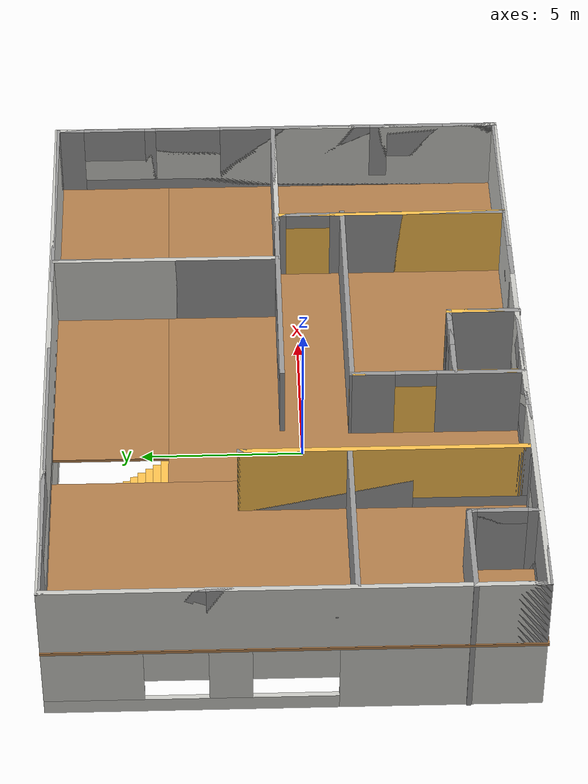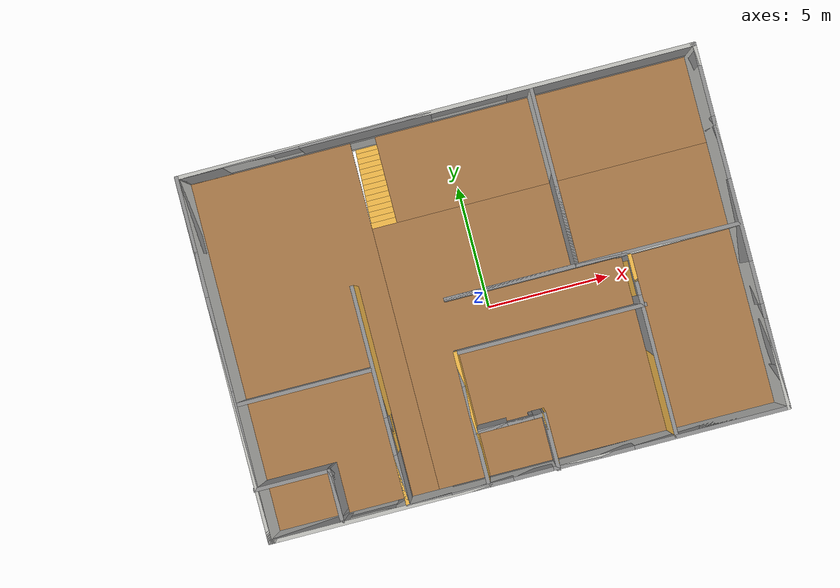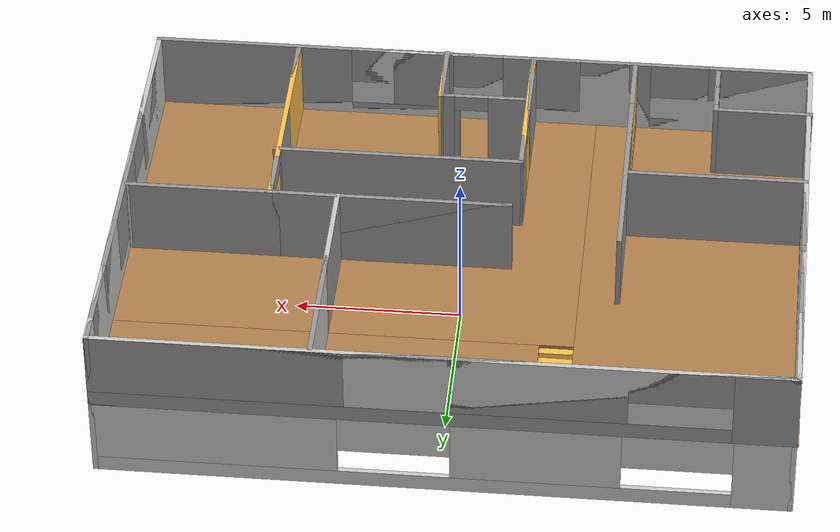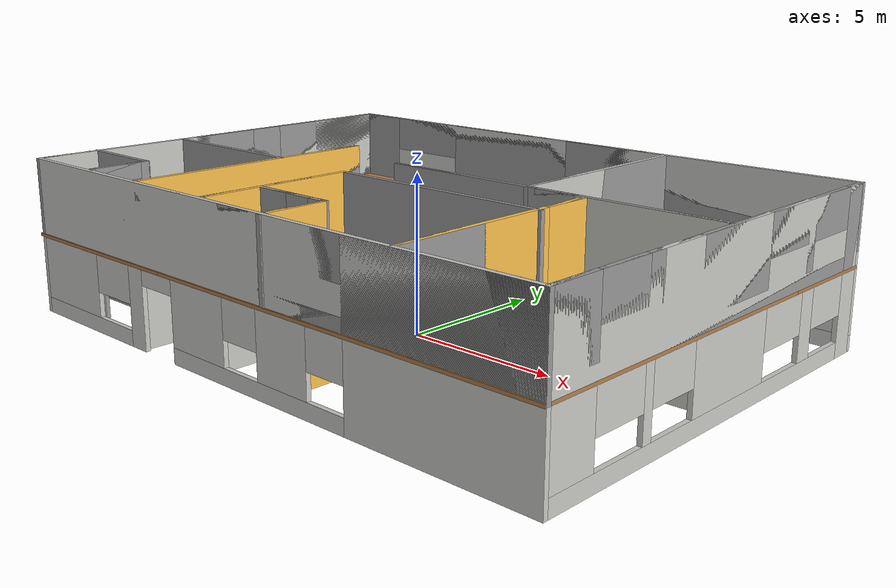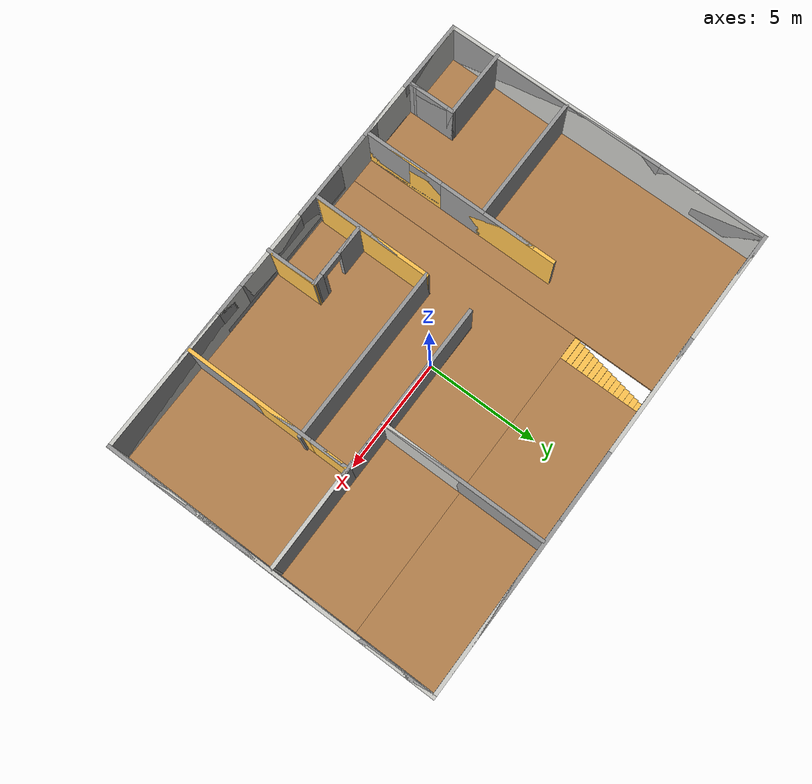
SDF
<?xml version='1.0'?>
<sdf version='1.6'>
  <model name='myProjectBuilding'>
    <pose frame=''>-0.140832 0.553642 0 0 -0 0</pose>
    <link name='Door_9'>
      <collision name='Door_9_Collision'>
        <geometry>
          <box>
            <size>1.41879 0.2 2</size>
          </box>
        </geometry>
        <pose frame=''>0 0 1 0 -0 0</pose>
      </collision>
      <visual name='Door_9_Visual'>
        <pose frame=''>0 0 1 0 -0 0</pose>
        <geometry>
          <box>
            <size>1.41879 0.2 2</size>
          </box>
        </geometry>
        <material>
          <script>
            <uri>file://media/materials/scripts/gazebo.material</uri>
            <name>Gazebo/Grey</name>
          </script>
        </material>
      </visual>
      <pose frame=''>4.70443 0.050341 0 0 -0 0</pose>
    </link>
    <link name='Floor_0'>
      <pose frame=''>-0 -1e-06 2.5 0 -0 0</pose>
      <visual name='Floor_0_Visual_0'>
        <pose frame=''>-6.8354 0 0.05 0 -0 0</pose>
        <geometry>
          <box>
            <size>6.61888 14.2917 0.1</size>
          </box>
        </geometry>
        <material>
          <script>
            <uri>file://media/materials/scripts/gazebo.material</uri>
            <name>Gazebo/Wood</name>
          </script>
          <ambient>1 1 1 1</ambient>
        </material>
        <meta>
          <layer>1</layer>
        </meta>
      </visual>
      <collision name='Floor_0_Collision_0'>
        <geometry>
          <box>
            <size>6.61888 14.2917 0.1</size>
          </box>
        </geometry>
        <pose frame=''>-6.8354 0 0.05 0 -0 0</pose>
      </collision>
      <visual name='Floor_0_Visual_1'>
        <pose frame=''>3.30944 -1.80065 0.05 0 -0 0</pose>
        <geometry>
          <box>
            <size>13.6708 10.6904 0.1</size>
          </box>
        </geometry>
        <material>
          <script>
            <uri>file://media/materials/scripts/gazebo.material</uri>
            <name>Gazebo/Wood</name>
          </script>
          <ambient>1 1 1 1</ambient>
        </material>
        <meta>
          <layer>1</layer>
        </meta>
      </visual>
      <collision name='Floor_0_Collision_1'>
        <geometry>
          <box>
            <size>13.6708 10.6904 0.1</size>
          </box>
        </geometry>
        <pose frame=''>3.30944 -1.80065 0.05 0 -0 0</pose>
      </collision>
      <visual name='Floor_0_Visual_2'>
        <pose frame=''>3.80944 5.3452 0.05 0 -0 0</pose>
        <geometry>
          <box>
            <size>12.6708 3.6013 0.1</size>
          </box>
        </geometry>
        <material>
          <script>
            <uri>file://media/materials/scripts/gazebo.material</uri>
            <name>Gazebo/Wood</name>
          </script>
          <ambient>1 1 1 1</ambient>
        </material>
        <meta>
          <layer>1</layer>
        </meta>
      </visual>
      <collision name='Floor_0_Collision_2'>
        <geometry>
          <box>
            <size>12.6708 3.6013 0.1</size>
          </box>
        </geometry>
        <pose frame=''>3.80944 5.3452 0.05 0 -0 0</pose>
      </collision>
      <visual name='Floor_0_Visual_3'>
        <pose frame=''>-3.02596 7.0952 0.05 0 -0 0</pose>
        <geometry>
          <box>
            <size>1 0.101297 0.1</size>
          </box>
        </geometry>
        <material>
          <script>
            <uri>file://media/materials/scripts/gazebo.material</uri>
            <name>Gazebo/Wood</name>
          </script>
          <ambient>1 1 1 1</ambient>
        </material>
        <meta>
          <layer>1</layer>
        </meta>
      </visual>
      <collision name='Floor_0_Collision_3'>
        <geometry>
          <box>
            <size>1 0.101297 0.1</size>
          </box>
        </geometry>
        <pose frame=''>-3.02596 7.0952 0.05 0 -0 0</pose>
      </collision>
    </link>
    <link name='Stairs_0'>
      <visual name='Stairs_0_Visual_0'>
        <pose frame=''>-3.02596 6.92788 0.083333 0 -0 0</pose>
        <geometry>
          <box>
            <size>1 0.233333 0.166667</size>
          </box>
        </geometry>
        <material>
          <script>
            <uri>file://media/materials/scripts/gazebo.material</uri>
            <name>Gazebo/Grey</name>
          </script>
          <ambient>1 0.764706 0.305882 1</ambient>
        </material>
        <meta>
          <layer>0</layer>
        </meta>
      </visual>
      <collision name='Stairs_0_Collision_0'>
        <geometry>
          <box>
            <size>1 0.233333 0.166667</size>
          </box>
        </geometry>
        <pose frame=''>-3.02596 6.92788 0.083333 0 -0 0</pose>
      </collision>
      <visual name='Stairs_0_Visual_1'>
        <pose frame=''>-3.02596 6.69455 0.25 0 -0 0</pose>
        <geometry>
          <box>
            <size>1 0.233333 0.166667</size>
          </box>
        </geometry>
        <material>
          <script>
            <uri>file://media/materials/scripts/gazebo.material</uri>
            <name>Gazebo/Grey</name>
          </script>
          <ambient>1 0.764706 0.305882 1</ambient>
        </material>
        <meta>
          <layer>0</layer>
        </meta>
      </visual>
      <collision name='Stairs_0_Collision_1'>
        <geometry>
          <box>
            <size>1 0.233333 0.166667</size>
          </box>
        </geometry>
        <pose frame=''>-3.02596 6.69455 0.25 0 -0 0</pose>
      </collision>
      <visual name='Stairs_0_Visual_2'>
        <pose frame=''>-3.02596 6.46122 0.416667 0 -0 0</pose>
        <geometry>
          <box>
            <size>1 0.233333 0.166667</size>
          </box>
        </geometry>
        <material>
          <script>
            <uri>file://media/materials/scripts/gazebo.material</uri>
            <name>Gazebo/Grey</name>
          </script>
          <ambient>1 0.764706 0.305882 1</ambient>
        </material>
        <meta>
          <layer>0</layer>
        </meta>
      </visual>
      <collision name='Stairs_0_Collision_2'>
        <geometry>
          <box>
            <size>1 0.233333 0.166667</size>
          </box>
        </geometry>
        <pose frame=''>-3.02596 6.46122 0.416667 0 -0 0</pose>
      </collision>
      <visual name='Stairs_0_Visual_3'>
        <pose frame=''>-3.02596 6.22788 0.583333 0 -0 0</pose>
        <geometry>
          <box>
            <size>1 0.233333 0.166667</size>
          </box>
        </geometry>
        <material>
          <script>
            <uri>file://media/materials/scripts/gazebo.material</uri>
            <name>Gazebo/Grey</name>
          </script>
          <ambient>1 0.764706 0.305882 1</ambient>
        </material>
        <meta>
          <layer>0</layer>
        </meta>
      </visual>
      <collision name='Stairs_0_Collision_3'>
        <geometry>
          <box>
            <size>1 0.233333 0.166667</size>
          </box>
        </geometry>
        <pose frame=''>-3.02596 6.22788 0.583333 0 -0 0</pose>
      </collision>
      <visual name='Stairs_0_Visual_4'>
        <pose frame=''>-3.02596 5.99455 0.75 0 -0 0</pose>
        <geometry>
          <box>
            <size>1 0.233333 0.166667</size>
          </box>
        </geometry>
        <material>
          <script>
            <uri>file://media/materials/scripts/gazebo.material</uri>
            <name>Gazebo/Grey</name>
          </script>
          <ambient>1 0.764706 0.305882 1</ambient>
        </material>
        <meta>
          <layer>0</layer>
        </meta>
      </visual>
      <collision name='Stairs_0_Collision_4'>
        <geometry>
          <box>
            <size>1 0.233333 0.166667</size>
          </box>
        </geometry>
        <pose frame=''>-3.02596 5.99455 0.75 0 -0 0</pose>
      </collision>
      <visual name='Stairs_0_Visual_5'>
        <pose frame=''>-3.02596 5.76122 0.916667 0 -0 0</pose>
        <geometry>
          <box>
            <size>1 0.233333 0.166667</size>
          </box>
        </geometry>
        <material>
          <script>
            <uri>file://media/materials/scripts/gazebo.material</uri>
            <name>Gazebo/Grey</name>
          </script>
          <ambient>1 0.764706 0.305882 1</ambient>
        </material>
        <meta>
          <layer>0</layer>
        </meta>
      </visual>
      <collision name='Stairs_0_Collision_5'>
        <geometry>
          <box>
            <size>1 0.233333 0.166667</size>
          </box>
        </geometry>
        <pose frame=''>-3.02596 5.76122 0.916667 0 -0 0</pose>
      </collision>
      <visual name='Stairs_0_Visual_6'>
        <pose frame=''>-3.02596 5.52788 1.08333 0 -0 0</pose>
        <geometry>
          <box>
            <size>1 0.233333 0.166667</size>
          </box>
        </geometry>
        <material>
          <script>
            <uri>file://media/materials/scripts/gazebo.material</uri>
            <name>Gazebo/Grey</name>
          </script>
          <ambient>1 0.764706 0.305882 1</ambient>
        </material>
        <meta>
          <layer>0</layer>
        </meta>
      </visual>
      <collision name='Stairs_0_Collision_6'>
        <geometry>
          <box>
            <size>1 0.233333 0.166667</size>
          </box>
        </geometry>
        <pose frame=''>-3.02596 5.52788 1.08333 0 -0 0</pose>
      </collision>
      <visual name='Stairs_0_Visual_7'>
        <pose frame=''>-3.02596 5.29455 1.25 0 -0 0</pose>
        <geometry>
          <box>
            <size>1 0.233333 0.166667</size>
          </box>
        </geometry>
        <material>
          <script>
            <uri>file://media/materials/scripts/gazebo.material</uri>
            <name>Gazebo/Grey</name>
          </script>
          <ambient>1 0.764706 0.305882 1</ambient>
        </material>
        <meta>
          <layer>0</layer>
        </meta>
      </visual>
      <collision name='Stairs_0_Collision_7'>
        <geometry>
          <box>
            <size>1 0.233333 0.166667</size>
          </box>
        </geometry>
        <pose frame=''>-3.02596 5.29455 1.25 0 -0 0</pose>
      </collision>
      <visual name='Stairs_0_Visual_8'>
        <pose frame=''>-3.02596 5.06122 1.41667 0 -0 0</pose>
        <geometry>
          <box>
            <size>1 0.233333 0.166667</size>
          </box>
        </geometry>
        <material>
          <script>
            <uri>file://media/materials/scripts/gazebo.material</uri>
            <name>Gazebo/Grey</name>
          </script>
          <ambient>1 0.764706 0.305882 1</ambient>
        </material>
        <meta>
          <layer>0</layer>
        </meta>
      </visual>
      <collision name='Stairs_0_Collision_8'>
        <geometry>
          <box>
            <size>1 0.233333 0.166667</size>
          </box>
        </geometry>
        <pose frame=''>-3.02596 5.06122 1.41667 0 -0 0</pose>
      </collision>
      <visual name='Stairs_0_Visual_9'>
        <pose frame=''>-3.02596 4.82788 1.58333 0 -0 0</pose>
        <geometry>
          <box>
            <size>1 0.233333 0.166667</size>
          </box>
        </geometry>
        <material>
          <script>
            <uri>file://media/materials/scripts/gazebo.material</uri>
            <name>Gazebo/Grey</name>
          </script>
          <ambient>1 0.764706 0.305882 1</ambient>
        </material>
        <meta>
          <layer>0</layer>
        </meta>
      </visual>
      <collision name='Stairs_0_Collision_9'>
        <geometry>
          <box>
            <size>1 0.233333 0.166667</size>
          </box>
        </geometry>
        <pose frame=''>-3.02596 4.82788 1.58333 0 -0 0</pose>
      </collision>
      <visual name='Stairs_0_Visual_10'>
        <pose frame=''>-3.02596 4.59455 1.75 0 -0 0</pose>
        <geometry>
          <box>
            <size>1 0.233333 0.166667</size>
          </box>
        </geometry>
        <material>
          <script>
            <uri>file://media/materials/scripts/gazebo.material</uri>
            <name>Gazebo/Grey</name>
          </script>
          <ambient>1 0.764706 0.305882 1</ambient>
        </material>
        <meta>
          <layer>0</layer>
        </meta>
      </visual>
      <collision name='Stairs_0_Collision_10'>
        <geometry>
          <box>
            <size>1 0.233333 0.166667</size>
          </box>
        </geometry>
        <pose frame=''>-3.02596 4.59455 1.75 0 -0 0</pose>
      </collision>
      <visual name='Stairs_0_Visual_11'>
        <pose frame=''>-3.02596 4.36122 1.91667 0 -0 0</pose>
        <geometry>
          <box>
            <size>1 0.233333 0.166667</size>
          </box>
        </geometry>
        <material>
          <script>
            <uri>file://media/materials/scripts/gazebo.material</uri>
            <name>Gazebo/Grey</name>
          </script>
          <ambient>1 0.764706 0.305882 1</ambient>
        </material>
        <meta>
          <layer>0</layer>
        </meta>
      </visual>
      <collision name='Stairs_0_Collision_11'>
        <geometry>
          <box>
            <size>1 0.233333 0.166667</size>
          </box>
        </geometry>
        <pose frame=''>-3.02596 4.36122 1.91667 0 -0 0</pose>
      </collision>
      <visual name='Stairs_0_Visual_12'>
        <pose frame=''>-3.02596 4.12788 2.08333 0 -0 0</pose>
        <geometry>
          <box>
            <size>1 0.233333 0.166667</size>
          </box>
        </geometry>
        <material>
          <script>
            <uri>file://media/materials/scripts/gazebo.material</uri>
            <name>Gazebo/Grey</name>
          </script>
          <ambient>1 0.764706 0.305882 1</ambient>
        </material>
        <meta>
          <layer>0</layer>
        </meta>
      </visual>
      <collision name='Stairs_0_Collision_12'>
        <geometry>
          <box>
            <size>1 0.233333 0.166667</size>
          </box>
        </geometry>
        <pose frame=''>-3.02596 4.12788 2.08333 0 -0 0</pose>
      </collision>
      <visual name='Stairs_0_Visual_13'>
        <pose frame=''>-3.02596 3.89455 2.25 0 -0 0</pose>
        <geometry>
          <box>
            <size>1 0.233333 0.166667</size>
          </box>
        </geometry>
        <material>
          <script>
            <uri>file://media/materials/scripts/gazebo.material</uri>
            <name>Gazebo/Grey</name>
          </script>
          <ambient>1 0.764706 0.305882 1</ambient>
        </material>
        <meta>
          <layer>0</layer>
        </meta>
      </visual>
      <collision name='Stairs_0_Collision_13'>
        <geometry>
          <box>
            <size>1 0.233333 0.166667</size>
          </box>
        </geometry>
        <pose frame=''>-3.02596 3.89455 2.25 0 -0 0</pose>
      </collision>
      <visual name='Stairs_0_Visual_14'>
        <pose frame=''>-3.02596 3.66122 2.41667 0 -0 0</pose>
        <geometry>
          <box>
            <size>1 0.233333 0.166667</size>
          </box>
        </geometry>
        <material>
          <script>
            <uri>file://media/materials/scripts/gazebo.material</uri>
            <name>Gazebo/Grey</name>
          </script>
          <ambient>1 0.764706 0.305882 1</ambient>
        </material>
        <meta>
          <layer>0</layer>
        </meta>
      </visual>
      <collision name='Stairs_0_Collision_14'>
        <geometry>
          <box>
            <size>1 0.233333 0.166667</size>
          </box>
        </geometry>
        <pose frame=''>-3.02596 3.66122 2.41667 0 -0 0</pose>
      </collision>
    </link>
    <link name='Wall_0'>
      <pose frame=''>0.019837 7.07085 0 0 -0 0</pose>
      <visual name='Wall_0_Visual_0'>
        <pose frame=''>-9.23411 0 1.25 0 -0 0</pose>
        <geometry>
          <box>
            <size>1.78178 0.15 2.5</size>
          </box>
        </geometry>
        <material>
          <script>
            <uri>file://media/materials/scripts/gazebo.material</uri>
            <name>Gazebo/CeilingTiled</name>
          </script>
          <ambient>1 1 1 1</ambient>
        </material>
        <meta>
          <layer>0</layer>
        </meta>
      </visual>
      <collision name='Wall_0_Collision_0'>
        <geometry>
          <box>
            <size>1.78178 0.15 2.5</size>
          </box>
        </geometry>
        <pose frame=''>-9.23411 0 1.25 0 -0 0</pose>
      </collision>
      <visual name='Wall_0_Visual_1'>
        <pose frame=''>0.890889 0 0.25 0 -0 0</pose>
        <geometry>
          <box>
            <size>18.4682 0.15 0.5</size>
          </box>
        </geometry>
        <material>
          <script>
            <uri>file://media/materials/scripts/gazebo.material</uri>
            <name>Gazebo/CeilingTiled</name>
          </script>
          <ambient>1 1 1 1</ambient>
        </material>
        <meta>
          <layer>0</layer>
        </meta>
      </visual>
      <collision name='Wall_0_Collision_1'>
        <geometry>
          <box>
            <size>18.4682 0.15 0.5</size>
          </box>
        </geometry>
        <pose frame=''>0.890889 0 0.25 0 -0 0</pose>
      </collision>
      <visual name='Wall_0_Visual_2'>
        <pose frame=''>-2.70341 0 1.5 0 -0 0</pose>
        <geometry>
          <box>
            <size>4.90672 0.15 2</size>
          </box>
        </geometry>
        <material>
          <script>
            <uri>file://media/materials/scripts/gazebo.material</uri>
            <name>Gazebo/CeilingTiled</name>
          </script>
          <ambient>1 1 1 1</ambient>
        </material>
        <meta>
          <layer>0</layer>
        </meta>
      </visual>
      <collision name='Wall_0_Collision_2'>
        <geometry>
          <box>
            <size>4.90672 0.15 2</size>
          </box>
        </geometry>
        <pose frame=''>-2.70341 0 1.5 0 -0 0</pose>
      </collision>
      <visual name='Wall_0_Visual_3'>
        <pose frame=''>6.55664 0 1.5 0 -0 0</pose>
        <geometry>
          <box>
            <size>7.13672 0.15 2</size>
          </box>
        </geometry>
        <material>
          <script>
            <uri>file://media/materials/scripts/gazebo.material</uri>
            <name>Gazebo/CeilingTiled</name>
          </script>
          <ambient>1 1 1 1</ambient>
        </material>
        <meta>
          <layer>0</layer>
        </meta>
      </visual>
      <collision name='Wall_0_Collision_3'>
        <geometry>
          <box>
            <size>7.13672 0.15 2</size>
          </box>
        </geometry>
        <pose frame=''>6.55664 0 1.5 0 -0 0</pose>
      </collision>
      <visual name='Wall_0_Visual_4'>
        <pose frame=''>-6.75 0 1.9 0 -0 0</pose>
        <geometry>
          <box>
            <size>3.18645 0.15 1.2</size>
          </box>
        </geometry>
        <material>
          <script>
            <uri>file://media/materials/scripts/gazebo.material</uri>
            <name>Gazebo/CeilingTiled</name>
          </script>
          <ambient>1 1 1 1</ambient>
        </material>
        <meta>
          <layer>0</layer>
        </meta>
      </visual>
      <collision name='Wall_0_Collision_4'>
        <geometry>
          <box>
            <size>3.18645 0.15 1.2</size>
          </box>
        </geometry>
        <pose frame=''>-6.75 0 1.9 0 -0 0</pose>
      </collision>
      <visual name='Wall_0_Visual_5'>
        <pose frame=''>1.36912 0 1.9 0 -0 0</pose>
        <geometry>
          <box>
            <size>3.23833 0.15 1.2</size>
          </box>
        </geometry>
        <material>
          <script>
            <uri>file://media/materials/scripts/gazebo.material</uri>
            <name>Gazebo/CeilingTiled</name>
          </script>
          <ambient>1 1 1 1</ambient>
        </material>
        <meta>
          <layer>0</layer>
        </meta>
      </visual>
      <collision name='Wall_0_Collision_5'>
        <geometry>
          <box>
            <size>3.23833 0.15 1.2</size>
          </box>
        </geometry>
        <pose frame=''>1.36912 0 1.9 0 -0 0</pose>
      </collision>
    </link>
    <link name='Wall_1'>
      <pose frame=''>10.0698 0.020848 0 0 -0 -1.5708</pose>
      <visual name='Wall_1_Visual_0'>
        <pose frame=''>-6.65077 0 1.25 0 -0 0</pose>
        <geometry>
          <box>
            <size>0.948468 0.15 2.5</size>
          </box>
        </geometry>
        <material>
          <script>
            <uri>file://media/materials/scripts/gazebo.material</uri>
            <name>Gazebo/CeilingTiled</name>
          </script>
          <ambient>1 1 1 1</ambient>
        </material>
        <meta>
          <layer>0</layer>
        </meta>
      </visual>
      <collision name='Wall_1_Collision_0'>
        <geometry>
          <box>
            <size>0.948468 0.15 2.5</size>
          </box>
        </geometry>
        <pose frame=''>-6.65077 0 1.25 0 -0 0</pose>
      </collision>
      <visual name='Wall_1_Visual_1'>
        <pose frame=''>0.474234 0 0.25 0 -0 0</pose>
        <geometry>
          <box>
            <size>13.3015 0.15 0.5</size>
          </box>
        </geometry>
        <material>
          <script>
            <uri>file://media/materials/scripts/gazebo.material</uri>
            <name>Gazebo/CeilingTiled</name>
          </script>
          <ambient>1 1 1 1</ambient>
        </material>
        <meta>
          <layer>0</layer>
        </meta>
      </visual>
      <collision name='Wall_1_Collision_1'>
        <geometry>
          <box>
            <size>13.3015 0.15 0.5</size>
          </box>
        </geometry>
        <pose frame=''>0.474234 0 0.25 0 -0 0</pose>
      </collision>
      <visual name='Wall_1_Visual_2'>
        <pose frame=''>-4.11639 0 1.5 0 -0 0</pose>
        <geometry>
          <box>
            <size>0.652621 0.15 2</size>
          </box>
        </geometry>
        <material>
          <script>
            <uri>file://media/materials/scripts/gazebo.material</uri>
            <name>Gazebo/CeilingTiled</name>
          </script>
          <ambient>1 1 1 1</ambient>
        </material>
        <meta>
          <layer>0</layer>
        </meta>
      </visual>
      <collision name='Wall_1_Collision_2'>
        <geometry>
          <box>
            <size>0.652621 0.15 2</size>
          </box>
        </geometry>
        <pose frame=''>-4.11639 0 1.5 0 -0 0</pose>
      </collision>
      <visual name='Wall_1_Visual_3'>
        <pose frame=''>-0.168769 0 1.5 0 -0 0</pose>
        <geometry>
          <box>
            <size>3.35994 0.15 2</size>
          </box>
        </geometry>
        <material>
          <script>
            <uri>file://media/materials/scripts/gazebo.material</uri>
            <name>Gazebo/CeilingTiled</name>
          </script>
          <ambient>1 1 1 1</ambient>
        </material>
        <meta>
          <layer>0</layer>
        </meta>
      </visual>
      <collision name='Wall_1_Collision_3'>
        <geometry>
          <box>
            <size>3.35994 0.15 2</size>
          </box>
        </geometry>
        <pose frame=''>-0.168769 0 1.5 0 -0 0</pose>
      </collision>
      <visual name='Wall_1_Visual_4'>
        <pose frame=''>3.42421 0 1.5 0 -0 0</pose>
        <geometry>
          <box>
            <size>0.342006 0.15 2</size>
          </box>
        </geometry>
        <material>
          <script>
            <uri>file://media/materials/scripts/gazebo.material</uri>
            <name>Gazebo/CeilingTiled</name>
          </script>
          <ambient>1 1 1 1</ambient>
        </material>
        <meta>
          <layer>0</layer>
        </meta>
      </visual>
      <collision name='Wall_1_Collision_4'>
        <geometry>
          <box>
            <size>0.342006 0.15 2</size>
          </box>
        </geometry>
        <pose frame=''>3.42421 0 1.5 0 -0 0</pose>
      </collision>
      <visual name='Wall_1_Visual_5'>
        <pose frame=''>6.27597 0 1.5 0 -0 0</pose>
        <geometry>
          <box>
            <size>1.69805 0.15 2</size>
          </box>
        </geometry>
        <material>
          <script>
            <uri>file://media/materials/scripts/gazebo.material</uri>
            <name>Gazebo/CeilingTiled</name>
          </script>
          <ambient>1 1 1 1</ambient>
        </material>
        <meta>
          <layer>0</layer>
        </meta>
      </visual>
      <collision name='Wall_1_Collision_5'>
        <geometry>
          <box>
            <size>1.69805 0.15 2</size>
          </box>
        </geometry>
        <pose frame=''>6.27597 0 1.5 0 -0 0</pose>
      </collision>
      <visual name='Wall_1_Visual_6'>
        <pose frame=''>-5.30962 0 1.9 0 -0 0</pose>
        <geometry>
          <box>
            <size>1.73383 0.15 1.2</size>
          </box>
        </geometry>
        <material>
          <script>
            <uri>file://media/materials/scripts/gazebo.material</uri>
            <name>Gazebo/CeilingTiled</name>
          </script>
          <ambient>1 1 1 1</ambient>
        </material>
        <meta>
          <layer>0</layer>
        </meta>
      </visual>
      <collision name='Wall_1_Collision_6'>
        <geometry>
          <box>
            <size>1.73383 0.15 1.2</size>
          </box>
        </geometry>
        <pose frame=''>-5.30962 0 1.9 0 -0 0</pose>
      </collision>
      <visual name='Wall_1_Visual_7'>
        <pose frame=''>-2.81941 0 1.9 0 -0 0</pose>
        <geometry>
          <box>
            <size>1.94135 0.15 1.2</size>
          </box>
        </geometry>
        <material>
          <script>
            <uri>file://media/materials/scripts/gazebo.material</uri>
            <name>Gazebo/CeilingTiled</name>
          </script>
          <ambient>1 1 1 1</ambient>
        </material>
        <meta>
          <layer>0</layer>
        </meta>
      </visual>
      <collision name='Wall_1_Collision_7'>
        <geometry>
          <box>
            <size>1.94135 0.15 1.2</size>
          </box>
        </geometry>
        <pose frame=''>-2.81941 0 1.9 0 -0 0</pose>
      </collision>
      <visual name='Wall_1_Visual_8'>
        <pose frame=''>2.38221 0 1.9 0 -0 0</pose>
        <geometry>
          <box>
            <size>1.74201 0.15 1.2</size>
          </box>
        </geometry>
        <material>
          <script>
            <uri>file://media/materials/scripts/gazebo.material</uri>
            <name>Gazebo/CeilingTiled</name>
          </script>
          <ambient>1 1 1 1</ambient>
        </material>
        <meta>
          <layer>0</layer>
        </meta>
      </visual>
      <collision name='Wall_1_Collision_8'>
        <geometry>
          <box>
            <size>1.74201 0.15 1.2</size>
          </box>
        </geometry>
        <pose frame=''>2.38221 0 1.9 0 -0 0</pose>
      </collision>
      <visual name='Wall_1_Visual_9'>
        <pose frame=''>4.51108 0 1.9 0 -0 0</pose>
        <geometry>
          <box>
            <size>1.83173 0.15 1.2</size>
          </box>
        </geometry>
        <material>
          <script>
            <uri>file://media/materials/scripts/gazebo.material</uri>
            <name>Gazebo/CeilingTiled</name>
          </script>
          <ambient>1 1 1 1</ambient>
        </material>
        <meta>
          <layer>0</layer>
        </meta>
      </visual>
      <collision name='Wall_1_Collision_9'>
        <geometry>
          <box>
            <size>1.83173 0.15 1.2</size>
          </box>
        </geometry>
        <pose frame=''>4.51108 0 1.9 0 -0 0</pose>
      </collision>
    </link>
    <link name='Wall_10'>
      <collision name='Wall_10_Collision'>
        <geometry>
          <box>
            <size>4.57812 0.15 2.5</size>
          </box>
        </geometry>
        <pose frame=''>0 0 1.25 0 -0 0</pose>
      </collision>
      <visual name='Wall_10_Visual'>
        <pose frame=''>0 0 1.25 0 -0 0</pose>
        <geometry>
          <box>
            <size>4.57812 0.15 2.5</size>
          </box>
        </geometry>
        <material>
          <script>
            <uri>file://media/materials/scripts/gazebo.material</uri>
            <name>Gazebo/CeilingTiled</name>
          </script>
          <ambient>1 1 1 1</ambient>
        </material>
        <meta>
          <layer>0</layer>
        </meta>
      </visual>
      <pose frame=''>7.6982 0.114753 0 0 -0 0.005858</pose>
    </link>
    <link name='Wall_103'>
      <pose frame=''>0.019837 7.07085 2.5 0 -0 0</pose>
      <visual name='Wall_103_Visual_0'>
        <pose frame=''>-9.19706 0 1.25 0 -0 0</pose>
        <geometry>
          <box>
            <size>1.85589 0.15 2.5</size>
          </box>
        </geometry>
        <material>
          <script>
            <uri>file://media/materials/scripts/gazebo.material</uri>
            <name>Gazebo/Grey</name>
          </script>
          <ambient>1 1 1 1</ambient>
        </material>
        <meta>
          <layer>1</layer>
        </meta>
      </visual>
      <collision name='Wall_103_Collision_0'>
        <geometry>
          <box>
            <size>1.85589 0.15 2.5</size>
          </box>
        </geometry>
        <pose frame=''>-9.19706 0 1.25 0 -0 0</pose>
      </collision>
      <visual name='Wall_103_Visual_1'>
        <pose frame=''>0.927944 0 0.25 0 -0 0</pose>
        <geometry>
          <box>
            <size>18.3941 0.15 0.5</size>
          </box>
        </geometry>
        <material>
          <script>
            <uri>file://media/materials/scripts/gazebo.material</uri>
            <name>Gazebo/Grey</name>
          </script>
          <ambient>1 1 1 1</ambient>
        </material>
        <meta>
          <layer>1</layer>
        </meta>
      </visual>
      <collision name='Wall_103_Collision_1'>
        <geometry>
          <box>
            <size>18.3941 0.15 0.5</size>
          </box>
        </geometry>
        <pose frame=''>0.927944 0 0.25 0 -0 0</pose>
      </collision>
      <visual name='Wall_103_Visual_2'>
        <pose frame=''>-2.75239 0 1.5 0 -0 0</pose>
        <geometry>
          <box>
            <size>5.10277 0.15 2</size>
          </box>
        </geometry>
        <material>
          <script>
            <uri>file://media/materials/scripts/gazebo.material</uri>
            <name>Gazebo/Grey</name>
          </script>
          <ambient>1 1 1 1</ambient>
        </material>
        <meta>
          <layer>1</layer>
        </meta>
      </visual>
      <collision name='Wall_103_Collision_2'>
        <geometry>
          <box>
            <size>5.10277 0.15 2</size>
          </box>
        </geometry>
        <pose frame=''>-2.75239 0 1.5 0 -0 0</pose>
      </collision>
      <visual name='Wall_103_Visual_3'>
        <pose frame=''>6.44467 0 1.5 0 -0 0</pose>
        <geometry>
          <box>
            <size>7.36067 0.15 2</size>
          </box>
        </geometry>
        <material>
          <script>
            <uri>file://media/materials/scripts/gazebo.material</uri>
            <name>Gazebo/Grey</name>
          </script>
          <ambient>1 1 1 1</ambient>
        </material>
        <meta>
          <layer>1</layer>
        </meta>
      </visual>
      <collision name='Wall_103_Collision_3'>
        <geometry>
          <box>
            <size>7.36067 0.15 2</size>
          </box>
        </geometry>
        <pose frame=''>6.44467 0 1.5 0 -0 0</pose>
      </collision>
      <visual name='Wall_103_Visual_4'>
        <pose frame=''>-6.78644 0 1.9 0 -0 0</pose>
        <geometry>
          <box>
            <size>2.96534 0.15 1.2</size>
          </box>
        </geometry>
        <material>
          <script>
            <uri>file://media/materials/scripts/gazebo.material</uri>
            <name>Gazebo/Grey</name>
          </script>
          <ambient>1 1 1 1</ambient>
        </material>
        <meta>
          <layer>1</layer>
        </meta>
      </visual>
      <collision name='Wall_103_Collision_4'>
        <geometry>
          <box>
            <size>2.96534 0.15 1.2</size>
          </box>
        </geometry>
        <pose frame=''>-6.78644 0 1.9 0 -0 0</pose>
      </collision>
      <visual name='Wall_103_Visual_5'>
        <pose frame=''>1.28167 0 1.9 0 -0 0</pose>
        <geometry>
          <box>
            <size>2.96534 0.15 1.2</size>
          </box>
        </geometry>
        <material>
          <script>
            <uri>file://media/materials/scripts/gazebo.material</uri>
            <name>Gazebo/Grey</name>
          </script>
          <ambient>1 1 1 1</ambient>
        </material>
        <meta>
          <layer>1</layer>
        </meta>
      </visual>
      <collision name='Wall_103_Collision_5'>
        <geometry>
          <box>
            <size>2.96534 0.15 1.2</size>
          </box>
        </geometry>
        <pose frame=''>1.28167 0 1.9 0 -0 0</pose>
      </collision>
    </link>
    <link name='Wall_104'>
      <pose frame=''>10.0698 0.020848 2.5 0 -0 -1.5708</pose>
      <visual name='Wall_104_Visual_0'>
        <pose frame=''>-6.6667 0 1.25 0 -0 0</pose>
        <geometry>
          <box>
            <size>0.916608 0.15 2.5</size>
          </box>
        </geometry>
        <material>
          <script>
            <uri>file://media/materials/scripts/gazebo.material</uri>
            <name>Gazebo/Grey</name>
          </script>
          <ambient>1 1 1 1</ambient>
        </material>
        <meta>
          <layer>1</layer>
        </meta>
      </visual>
      <collision name='Wall_104_Collision_0'>
        <geometry>
          <box>
            <size>0.916608 0.15 2.5</size>
          </box>
        </geometry>
        <pose frame=''>-6.6667 0 1.25 0 -0 0</pose>
      </collision>
      <visual name='Wall_104_Visual_1'>
        <pose frame=''>0.458304 0 0.25 0 -0 0</pose>
        <geometry>
          <box>
            <size>13.3334 0.15 0.5</size>
          </box>
        </geometry>
        <material>
          <script>
            <uri>file://media/materials/scripts/gazebo.material</uri>
            <name>Gazebo/Grey</name>
          </script>
          <ambient>1 1 1 1</ambient>
        </material>
        <meta>
          <layer>1</layer>
        </meta>
      </visual>
      <collision name='Wall_104_Collision_1'>
        <geometry>
          <box>
            <size>13.3334 0.15 0.5</size>
          </box>
        </geometry>
        <pose frame=''>0.458304 0 0.25 0 -0 0</pose>
      </collision>
      <visual name='Wall_104_Visual_2'>
        <pose frame=''>-4.07315 0 1.5 0 -0 0</pose>
        <geometry>
          <box>
            <size>0.356824 0.15 2</size>
          </box>
        </geometry>
        <material>
          <script>
            <uri>file://media/materials/scripts/gazebo.material</uri>
            <name>Gazebo/Grey</name>
          </script>
          <ambient>1 1 1 1</ambient>
        </material>
        <meta>
          <layer>1</layer>
        </meta>
      </visual>
      <collision name='Wall_104_Collision_2'>
        <geometry>
          <box>
            <size>0.356824 0.15 2</size>
          </box>
        </geometry>
        <pose frame=''>-4.07315 0 1.5 0 -0 0</pose>
      </collision>
      <visual name='Wall_104_Visual_3'>
        <pose frame=''>-0.222028 0 1.5 0 -0 0</pose>
        <geometry>
          <box>
            <size>3.19448 0.15 2</size>
          </box>
        </geometry>
        <material>
          <script>
            <uri>file://media/materials/scripts/gazebo.material</uri>
            <name>Gazebo/Grey</name>
          </script>
          <ambient>1 1 1 1</ambient>
        </material>
        <meta>
          <layer>1</layer>
        </meta>
      </visual>
      <collision name='Wall_104_Collision_3'>
        <geometry>
          <box>
            <size>3.19448 0.15 2</size>
          </box>
        </geometry>
        <pose frame=''>-0.222028 0 1.5 0 -0 0</pose>
      </collision>
      <visual name='Wall_104_Visual_4'>
        <pose frame=''>3.31023 0 1.5 0 -0 0</pose>
        <geometry>
          <box>
            <size>0.56446 0.15 2</size>
          </box>
        </geometry>
        <material>
          <script>
            <uri>file://media/materials/scripts/gazebo.material</uri>
            <name>Gazebo/Grey</name>
          </script>
          <ambient>1 1 1 1</ambient>
        </material>
        <meta>
          <layer>1</layer>
        </meta>
      </visual>
      <collision name='Wall_104_Collision_4'>
        <geometry>
          <box>
            <size>0.56446 0.15 2</size>
          </box>
        </geometry>
        <pose frame=''>3.31023 0 1.5 0 -0 0</pose>
      </collision>
      <visual name='Wall_104_Visual_5'>
        <pose frame=''>6.25335 0 1.5 0 -0 0</pose>
        <geometry>
          <box>
            <size>1.74331 0.15 2</size>
          </box>
        </geometry>
        <material>
          <script>
            <uri>file://media/materials/scripts/gazebo.material</uri>
            <name>Gazebo/Grey</name>
          </script>
          <ambient>1 1 1 1</ambient>
        </material>
        <meta>
          <layer>1</layer>
        </meta>
      </visual>
      <collision name='Wall_104_Collision_5'>
        <geometry>
          <box>
            <size>1.74331 0.15 2</size>
          </box>
        </geometry>
        <pose frame=''>6.25335 0 1.5 0 -0 0</pose>
      </collision>
      <visual name='Wall_104_Visual_6'>
        <pose frame=''>-5.22998 0 1.9 0 -0 0</pose>
        <geometry>
          <box>
            <size>1.95682 0.15 1.2</size>
          </box>
        </geometry>
        <material>
          <script>
            <uri>file://media/materials/scripts/gazebo.material</uri>
            <name>Gazebo/Grey</name>
          </script>
          <ambient>1 1 1 1</ambient>
        </material>
        <meta>
          <layer>1</layer>
        </meta>
      </visual>
      <collision name='Wall_104_Collision_6'>
        <geometry>
          <box>
            <size>1.95682 0.15 1.2</size>
          </box>
        </geometry>
        <pose frame=''>-5.22998 0 1.9 0 -0 0</pose>
      </collision>
      <visual name='Wall_104_Visual_7'>
        <pose frame=''>-2.85701 0 1.9 0 -0 0</pose>
        <geometry>
          <box>
            <size>2.07547 0.15 1.2</size>
          </box>
        </geometry>
        <material>
          <script>
            <uri>file://media/materials/scripts/gazebo.material</uri>
            <name>Gazebo/Grey</name>
          </script>
          <ambient>1 1 1 1</ambient>
        </material>
        <meta>
          <layer>1</layer>
        </meta>
      </visual>
      <collision name='Wall_104_Collision_7'>
        <geometry>
          <box>
            <size>2.07547 0.15 1.2</size>
          </box>
        </geometry>
        <pose frame=''>-2.85701 0 1.9 0 -0 0</pose>
      </collision>
      <visual name='Wall_104_Visual_8'>
        <pose frame=''>2.20161 0 1.9 0 -0 0</pose>
        <geometry>
          <box>
            <size>1.65279 0.15 1.2</size>
          </box>
        </geometry>
        <material>
          <script>
            <uri>file://media/materials/scripts/gazebo.material</uri>
            <name>Gazebo/Grey</name>
          </script>
          <ambient>1 1 1 1</ambient>
        </material>
        <meta>
          <layer>1</layer>
        </meta>
      </visual>
      <collision name='Wall_104_Collision_8'>
        <geometry>
          <box>
            <size>1.65279 0.15 1.2</size>
          </box>
        </geometry>
        <pose frame=''>2.20161 0 1.9 0 -0 0</pose>
      </collision>
      <visual name='Wall_104_Visual_9'>
        <pose frame=''>4.48708 0 1.9 0 -0 0</pose>
        <geometry>
          <box>
            <size>1.78923 0.15 1.2</size>
          </box>
        </geometry>
        <material>
          <script>
            <uri>file://media/materials/scripts/gazebo.material</uri>
            <name>Gazebo/Grey</name>
          </script>
          <ambient>1 1 1 1</ambient>
        </material>
        <meta>
          <layer>1</layer>
        </meta>
      </visual>
      <collision name='Wall_104_Collision_9'>
        <geometry>
          <box>
            <size>1.78923 0.15 1.2</size>
          </box>
        </geometry>
        <pose frame=''>4.48708 0 1.9 0 -0 0</pose>
      </collision>
    </link>
    <link name='Wall_105'>
      <pose frame=''>0.019837 -7.02915 2.5 0 -0 3.14159</pose>
      <visual name='Wall_105_Visual_0'>
        <pose frame=''>-7.09724 0 1.25 0 -0 0</pose>
        <geometry>
          <box>
            <size>6.05553 0.15 2.5</size>
          </box>
        </geometry>
        <material>
          <script>
            <uri>file://media/materials/scripts/gazebo.material</uri>
            <name>Gazebo/Grey</name>
          </script>
          <ambient>1 1 1 1</ambient>
        </material>
        <meta>
          <layer>1</layer>
        </meta>
      </visual>
      <collision name='Wall_105_Collision_0'>
        <geometry>
          <box>
            <size>6.05553 0.15 2.5</size>
          </box>
        </geometry>
        <pose frame=''>-7.09724 0 1.25 0 -0 0</pose>
      </collision>
      <visual name='Wall_105_Visual_1'>
        <pose frame=''>4.8469 0 1.25 0 -0 0</pose>
        <geometry>
          <box>
            <size>0.658901 0.15 2.5</size>
          </box>
        </geometry>
        <material>
          <script>
            <uri>file://media/materials/scripts/gazebo.material</uri>
            <name>Gazebo/Grey</name>
          </script>
          <ambient>1 1 1 1</ambient>
        </material>
        <meta>
          <layer>1</layer>
        </meta>
      </visual>
      <collision name='Wall_105_Collision_1'>
        <geometry>
          <box>
            <size>0.658901 0.15 2.5</size>
          </box>
        </geometry>
        <pose frame=''>4.8469 0 1.25 0 -0 0</pose>
      </collision>
      <visual name='Wall_105_Visual_2'>
        <pose frame=''>-0.53553 0 0.25 0 -0 0</pose>
        <geometry>
          <box>
            <size>7.06788 0.15 0.5</size>
          </box>
        </geometry>
        <material>
          <script>
            <uri>file://media/materials/scripts/gazebo.material</uri>
            <name>Gazebo/Grey</name>
          </script>
          <ambient>1 1 1 1</ambient>
        </material>
        <meta>
          <layer>1</layer>
        </meta>
      </visual>
      <collision name='Wall_105_Collision_2'>
        <geometry>
          <box>
            <size>7.06788 0.15 0.5</size>
          </box>
        </geometry>
        <pose frame=''>-0.53553 0 0.25 0 -0 0</pose>
      </collision>
      <visual name='Wall_105_Visual_3'>
        <pose frame=''>7.65067 0 0.25 0 -0 0</pose>
        <geometry>
          <box>
            <size>4.94865 0.15 0.5</size>
          </box>
        </geometry>
        <material>
          <script>
            <uri>file://media/materials/scripts/gazebo.material</uri>
            <name>Gazebo/Grey</name>
          </script>
          <ambient>1 1 1 1</ambient>
        </material>
        <meta>
          <layer>1</layer>
        </meta>
      </visual>
      <collision name='Wall_105_Collision_3'>
        <geometry>
          <box>
            <size>4.94865 0.15 0.5</size>
          </box>
        </geometry>
        <pose frame=''>7.65067 0 0.25 0 -0 0</pose>
      </collision>
      <visual name='Wall_105_Visual_4'>
        <pose frame=''>-1.84525 0 1.5 0 -0 0</pose>
        <geometry>
          <box>
            <size>1.83993 0.15 2</size>
          </box>
        </geometry>
        <material>
          <script>
            <uri>file://media/materials/scripts/gazebo.material</uri>
            <name>Gazebo/Grey</name>
          </script>
          <ambient>1 1 1 1</ambient>
        </material>
        <meta>
          <layer>1</layer>
        </meta>
      </visual>
      <collision name='Wall_105_Collision_4'>
        <geometry>
          <box>
            <size>1.83993 0.15 2</size>
          </box>
        </geometry>
        <pose frame=''>-1.84525 0 1.5 0 -0 0</pose>
      </collision>
      <visual name='Wall_105_Visual_5'>
        <pose frame=''>1.80734 0 1.5 0 -0 0</pose>
        <geometry>
          <box>
            <size>2.38213 0.15 2</size>
          </box>
        </geometry>
        <material>
          <script>
            <uri>file://media/materials/scripts/gazebo.material</uri>
            <name>Gazebo/Grey</name>
          </script>
          <ambient>1 1 1 1</ambient>
        </material>
        <meta>
          <layer>1</layer>
        </meta>
      </visual>
      <collision name='Wall_105_Collision_5'>
        <geometry>
          <box>
            <size>2.38213 0.15 2</size>
          </box>
        </geometry>
        <pose frame=''>1.80734 0 1.5 0 -0 0</pose>
      </collision>
      <visual name='Wall_105_Visual_6'>
        <pose frame=''>1.80734 0 1.5 0 -0 0</pose>
        <geometry>
          <box>
            <size>2.38213 0.15 2</size>
          </box>
        </geometry>
        <material>
          <script>
            <uri>file://media/materials/scripts/gazebo.material</uri>
            <name>Gazebo/Grey</name>
          </script>
          <ambient>1 1 1 1</ambient>
        </material>
        <meta>
          <layer>1</layer>
        </meta>
      </visual>
      <collision name='Wall_105_Collision_6'>
        <geometry>
          <box>
            <size>2.38213 0.15 2</size>
          </box>
        </geometry>
        <pose frame=''>1.80734 0 1.5 0 -0 0</pose>
      </collision>
      <visual name='Wall_105_Visual_7'>
        <pose frame=''>8.54074 0 1.5 0 -0 0</pose>
        <geometry>
          <box>
            <size>3.16851 0.15 2</size>
          </box>
        </geometry>
        <material>
          <script>
            <uri>file://media/materials/scripts/gazebo.material</uri>
            <name>Gazebo/Grey</name>
          </script>
          <ambient>1 1 1 1</ambient>
        </material>
        <meta>
          <layer>1</layer>
        </meta>
      </visual>
      <collision name='Wall_105_Collision_7'>
        <geometry>
          <box>
            <size>3.16851 0.15 2</size>
          </box>
        </geometry>
        <pose frame=''>8.54074 0 1.5 0 -0 0</pose>
      </collision>
      <visual name='Wall_105_Visual_8'>
        <pose frame=''>-3.41734 0 1.9 0 -0 0</pose>
        <geometry>
          <box>
            <size>1.30426 0.15 1.2</size>
          </box>
        </geometry>
        <material>
          <script>
            <uri>file://media/materials/scripts/gazebo.material</uri>
            <name>Gazebo/Grey</name>
          </script>
          <ambient>1 1 1 1</ambient>
        </material>
        <meta>
          <layer>1</layer>
        </meta>
      </visual>
      <collision name='Wall_105_Collision_8'>
        <geometry>
          <box>
            <size>1.30426 0.15 1.2</size>
          </box>
        </geometry>
        <pose frame=''>-3.41734 0 1.9 0 -0 0</pose>
      </collision>
      <visual name='Wall_105_Visual_9'>
        <pose frame=''>6.06642 0 1.9 0 -0 0</pose>
        <geometry>
          <box>
            <size>1.78014 0.15 1.2</size>
          </box>
        </geometry>
        <material>
          <script>
            <uri>file://media/materials/scripts/gazebo.material</uri>
            <name>Gazebo/Grey</name>
          </script>
          <ambient>1 1 1 1</ambient>
        </material>
        <meta>
          <layer>1</layer>
        </meta>
      </visual>
      <collision name='Wall_105_Collision_9'>
        <geometry>
          <box>
            <size>1.78014 0.15 1.2</size>
          </box>
        </geometry>
        <pose frame=''>6.06642 0 1.9 0 -0 0</pose>
      </collision>
      <visual name='Wall_105_Visual_10'>
        <pose frame=''>-0.154503 0 1.9 0 -0 0</pose>
        <geometry>
          <box>
            <size>1.54155 0.15 1.2</size>
          </box>
        </geometry>
        <material>
          <script>
            <uri>file://media/materials/scripts/gazebo.material</uri>
            <name>Gazebo/Grey</name>
          </script>
          <ambient>1 1 1 1</ambient>
        </material>
        <meta>
          <layer>1</layer>
        </meta>
      </visual>
      <collision name='Wall_105_Collision_10'>
        <geometry>
          <box>
            <size>1.54155 0.15 1.2</size>
          </box>
        </geometry>
        <pose frame=''>-0.154503 0 1.9 0 -0 0</pose>
      </collision>
      <visual name='Wall_105_Visual_11'>
        <pose frame=''>3.75793 0 2.25 0 -0 0</pose>
        <geometry>
          <box>
            <size>1.51904 0.15 0.5</size>
          </box>
        </geometry>
        <material>
          <script>
            <uri>file://media/materials/scripts/gazebo.material</uri>
            <name>Gazebo/Grey</name>
          </script>
          <ambient>1 1 1 1</ambient>
        </material>
        <meta>
          <layer>1</layer>
        </meta>
      </visual>
      <collision name='Wall_105_Collision_11'>
        <geometry>
          <box>
            <size>1.51904 0.15 0.5</size>
          </box>
        </geometry>
        <pose frame=''>3.75793 0 2.25 0 -0 0</pose>
      </collision>
      <visual name='Wall_105_Visual_12'>
        <pose frame=''>3.75793 0 2.25 0 -0 0</pose>
        <geometry>
          <box>
            <size>1.51904 0.15 0.5</size>
          </box>
        </geometry>
        <material>
          <script>
            <uri>file://media/materials/scripts/gazebo.material</uri>
            <name>Gazebo/Grey</name>
          </script>
          <ambient>1 1 1 1</ambient>
        </material>
        <meta>
          <layer>1</layer>
        </meta>
      </visual>
      <collision name='Wall_105_Collision_12'>
        <geometry>
          <box>
            <size>1.51904 0.15 0.5</size>
          </box>
        </geometry>
        <pose frame=''>3.75793 0 2.25 0 -0 0</pose>
      </collision>
    </link>
    <link name='Wall_106'>
      <pose frame=''>-10.0302 0.020848 2.5 0 -0 1.5708</pose>
      <visual name='Wall_106_Visual_0'>
        <pose frame=''>-4.18101 0 1.25 0 -0 0</pose>
        <geometry>
          <box>
            <size>5.88798 0.15 2.5</size>
          </box>
        </geometry>
        <material>
          <script>
            <uri>file://media/materials/scripts/gazebo.material</uri>
            <name>Gazebo/Grey</name>
          </script>
          <ambient>1 1 1 1</ambient>
        </material>
        <meta>
          <layer>1</layer>
        </meta>
      </visual>
      <collision name='Wall_106_Collision_0'>
        <geometry>
          <box>
            <size>5.88798 0.15 2.5</size>
          </box>
        </geometry>
        <pose frame=''>-4.18101 0 1.25 0 -0 0</pose>
      </collision>
      <visual name='Wall_106_Visual_1'>
        <pose frame=''>2.94399 0 0.25 0 -0 0</pose>
        <geometry>
          <box>
            <size>8.36202 0.15 0.5</size>
          </box>
        </geometry>
        <material>
          <script>
            <uri>file://media/materials/scripts/gazebo.material</uri>
            <name>Gazebo/Grey</name>
          </script>
          <ambient>1 1 1 1</ambient>
        </material>
        <meta>
          <layer>1</layer>
        </meta>
      </visual>
      <collision name='Wall_106_Collision_1'>
        <geometry>
          <box>
            <size>8.36202 0.15 0.5</size>
          </box>
        </geometry>
        <pose frame=''>2.94399 0 0.25 0 -0 0</pose>
      </collision>
      <visual name='Wall_106_Visual_2'>
        <pose frame=''>1.81803 0 1.5 0 -0 0</pose>
        <geometry>
          <box>
            <size>1.21997 0.15 2</size>
          </box>
        </geometry>
        <material>
          <script>
            <uri>file://media/materials/scripts/gazebo.material</uri>
            <name>Gazebo/Grey</name>
          </script>
          <ambient>1 1 1 1</ambient>
        </material>
        <meta>
          <layer>1</layer>
        </meta>
      </visual>
      <collision name='Wall_106_Collision_2'>
        <geometry>
          <box>
            <size>1.21997 0.15 2</size>
          </box>
        </geometry>
        <pose frame=''>1.81803 0 1.5 0 -0 0</pose>
      </collision>
      <visual name='Wall_106_Visual_3'>
        <pose frame=''>5.65137 0 1.5 0 -0 0</pose>
        <geometry>
          <box>
            <size>2.94726 0.15 2</size>
          </box>
        </geometry>
        <material>
          <script>
            <uri>file://media/materials/scripts/gazebo.material</uri>
            <name>Gazebo/Grey</name>
          </script>
          <ambient>1 1 1 1</ambient>
        </material>
        <meta>
          <layer>1</layer>
        </meta>
      </visual>
      <collision name='Wall_106_Collision_3'>
        <geometry>
          <box>
            <size>2.94726 0.15 2</size>
          </box>
        </geometry>
        <pose frame=''>5.65137 0 1.5 0 -0 0</pose>
      </collision>
      <visual name='Wall_106_Visual_4'>
        <pose frame=''>-0.014489 0 1.9 0 -0 0</pose>
        <geometry>
          <box>
            <size>2.44507 0.15 1.2</size>
          </box>
        </geometry>
        <material>
          <script>
            <uri>file://media/materials/scripts/gazebo.material</uri>
            <name>Gazebo/Grey</name>
          </script>
          <ambient>1 1 1 1</ambient>
        </material>
        <meta>
          <layer>1</layer>
        </meta>
      </visual>
      <collision name='Wall_106_Collision_4'>
        <geometry>
          <box>
            <size>2.44507 0.15 1.2</size>
          </box>
        </geometry>
        <pose frame=''>-0.014489 0 1.9 0 -0 0</pose>
      </collision>
      <visual name='Wall_106_Visual_5'>
        <pose frame=''>3.30288 0 1.9 0 -0 0</pose>
        <geometry>
          <box>
            <size>1.74973 0.15 1.2</size>
          </box>
        </geometry>
        <material>
          <script>
            <uri>file://media/materials/scripts/gazebo.material</uri>
            <name>Gazebo/Grey</name>
          </script>
          <ambient>1 1 1 1</ambient>
        </material>
        <meta>
          <layer>1</layer>
        </meta>
      </visual>
      <collision name='Wall_106_Collision_5'>
        <geometry>
          <box>
            <size>1.74973 0.15 1.2</size>
          </box>
        </geometry>
        <pose frame=''>3.30288 0 1.9 0 -0 0</pose>
      </collision>
    </link>
    <link name='Wall_108'>
      <collision name='Wall_108_Collision'>
        <geometry>
          <box>
            <size>5.5 0.15 2.5</size>
          </box>
        </geometry>
        <pose frame=''>0 0 1.25 0 -0 0</pose>
      </collision>
      <visual name='Wall_108_Visual'>
        <pose frame=''>0 0 1.25 0 -0 0</pose>
        <geometry>
          <box>
            <size>5.5 0.15 2.5</size>
          </box>
        </geometry>
        <material>
          <script>
            <uri>file://media/materials/scripts/gazebo.material</uri>
            <name>Gazebo/Grey</name>
          </script>
          <ambient>1 1 1 1</ambient>
        </material>
        <meta>
          <layer>1</layer>
        </meta>
      </visual>
      <pose frame=''>-7.35516 -1.737 2.5 0 -0 0</pose>
    </link>
    <link name='Wall_110'>
      <pose frame=''>-4.67404 -2.738 2.5 0 -0 -1.5708</pose>
      <visual name='Wall_110_Visual_0'>
        <pose frame=''>-1.69288 0 1.25 0 -0 0</pose>
        <geometry>
          <box>
            <size>5.11425 0.15 2.5</size>
          </box>
        </geometry>
        <material>
          <script>
            <uri>file://media/materials/scripts/gazebo.material</uri>
            <name>Gazebo/Grey</name>
          </script>
          <ambient>1 1 1 1</ambient>
        </material>
        <meta>
          <layer>1</layer>
        </meta>
      </visual>
      <collision name='Wall_110_Collision_0'>
        <geometry>
          <box>
            <size>5.11425 0.15 2.5</size>
          </box>
        </geometry>
        <pose frame=''>-1.69288 0 1.25 0 -0 0</pose>
      </collision>
      <visual name='Wall_110_Visual_1'>
        <pose frame=''>2.55712 0 0.25 0 -0 0</pose>
        <geometry>
          <box>
            <size>3.38576 0.15 0.5</size>
          </box>
        </geometry>
        <material>
          <script>
            <uri>file://media/materials/scripts/gazebo.material</uri>
            <name>Gazebo/Grey</name>
          </script>
          <ambient>1 1 1 1</ambient>
        </material>
        <meta>
          <layer>1</layer>
        </meta>
      </visual>
      <collision name='Wall_110_Collision_1'>
        <geometry>
          <box>
            <size>3.38576 0.15 0.5</size>
          </box>
        </geometry>
        <pose frame=''>2.55712 0 0.25 0 -0 0</pose>
      </collision>
      <visual name='Wall_110_Visual_2'>
        <pose frame=''>3.27954 0 1.5 0 -0 0</pose>
        <geometry>
          <box>
            <size>1.94093 0.15 2</size>
          </box>
        </geometry>
        <material>
          <script>
            <uri>file://media/materials/scripts/gazebo.material</uri>
            <name>Gazebo/Grey</name>
          </script>
          <ambient>1 1 1 1</ambient>
        </material>
        <meta>
          <layer>1</layer>
        </meta>
      </visual>
      <collision name='Wall_110_Collision_2'>
        <geometry>
          <box>
            <size>1.94093 0.15 2</size>
          </box>
        </geometry>
        <pose frame=''>3.27954 0 1.5 0 -0 0</pose>
      </collision>
      <visual name='Wall_110_Visual_3'>
        <pose frame=''>1.58666 0 1.9 0 -0 0</pose>
        <geometry>
          <box>
            <size>1.44483 0.15 1.2</size>
          </box>
        </geometry>
        <material>
          <script>
            <uri>file://media/materials/scripts/gazebo.material</uri>
            <name>Gazebo/Grey</name>
          </script>
          <ambient>1 1 1 1</ambient>
        </material>
        <meta>
          <layer>1</layer>
        </meta>
      </visual>
      <collision name='Wall_110_Collision_3'>
        <geometry>
          <box>
            <size>1.44483 0.15 1.2</size>
          </box>
        </geometry>
        <pose frame=''>1.58666 0 1.9 0 -0 0</pose>
      </collision>
    </link>
    <link name='Wall_112'>
      <pose frame=''>4.29399 0.127723 2.5 0 -0 0</pose>
      <visual name='Wall_112_Visual_0'>
        <pose frame=''>-3.00932 0 1.25 0 -0 0</pose>
        <geometry>
          <box>
            <size>5.48137 0.15 2.5</size>
          </box>
        </geometry>
        <material>
          <script>
            <uri>file://media/materials/scripts/gazebo.material</uri>
            <name>Gazebo/Grey</name>
          </script>
          <ambient>1 1 1 1</ambient>
        </material>
        <meta>
          <layer>1</layer>
        </meta>
      </visual>
      <collision name='Wall_112_Collision_0'>
        <geometry>
          <box>
            <size>5.48137 0.15 2.5</size>
          </box>
        </geometry>
        <pose frame=''>-3.00932 0 1.25 0 -0 0</pose>
      </collision>
      <visual name='Wall_112_Visual_1'>
        <pose frame=''>3.45764 0 1.25 0 -0 0</pose>
        <geometry>
          <box>
            <size>4.58472 0.15 2.5</size>
          </box>
        </geometry>
        <material>
          <script>
            <uri>file://media/materials/scripts/gazebo.material</uri>
            <name>Gazebo/Grey</name>
          </script>
          <ambient>1 1 1 1</ambient>
        </material>
        <meta>
          <layer>1</layer>
        </meta>
      </visual>
      <collision name='Wall_112_Collision_1'>
        <geometry>
          <box>
            <size>4.58472 0.15 2.5</size>
          </box>
        </geometry>
        <pose frame=''>3.45764 0 1.25 0 -0 0</pose>
      </collision>
      <visual name='Wall_112_Visual_2'>
        <pose frame=''>0.448326 0 2.25 0 -0 0</pose>
        <geometry>
          <box>
            <size>1.43392 0.15 0.5</size>
          </box>
        </geometry>
        <material>
          <script>
            <uri>file://media/materials/scripts/gazebo.material</uri>
            <name>Gazebo/Grey</name>
          </script>
          <ambient>1 1 1 1</ambient>
        </material>
        <meta>
          <layer>1</layer>
        </meta>
      </visual>
      <collision name='Wall_112_Collision_2'>
        <geometry>
          <box>
            <size>1.43392 0.15 0.5</size>
          </box>
        </geometry>
        <pose frame=''>0.448326 0 2.25 0 -0 0</pose>
      </collision>
    </link>
    <link name='Wall_119'>
      <collision name='Wall_119_Collision'>
        <geometry>
          <box>
            <size>7 0.15 2.5</size>
          </box>
        </geometry>
        <pose frame=''>0 0 1.25 0 -0 0</pose>
      </collision>
      <visual name='Wall_119_Visual'>
        <pose frame=''>0 0 1.25 0 -0 0</pose>
        <geometry>
          <box>
            <size>7 0.15 2.5</size>
          </box>
        </geometry>
        <material>
          <script>
            <uri>file://media/materials/scripts/gazebo.material</uri>
            <name>Gazebo/Grey</name>
          </script>
          <ambient>1 1 1 1</ambient>
        </material>
        <meta>
          <layer>1</layer>
        </meta>
      </visual>
      <pose frame=''>3.71899 3.55272 2.5 0 -0 -1.5708</pose>
    </link>
    <link name='Wall_12'>
      <collision name='Wall_12_Collision'>
        <geometry>
          <box>
            <size>5.5 0.15 2.5</size>
          </box>
        </geometry>
        <pose frame=''>0 0 1.25 0 -0 0</pose>
      </collision>
      <visual name='Wall_12_Visual'>
        <pose frame=''>0 0 1.25 0 -0 0</pose>
        <geometry>
          <box>
            <size>5.5 0.15 2.5</size>
          </box>
        </geometry>
        <material>
          <script>
            <uri>file://media/materials/scripts/gazebo.material</uri>
            <name>Gazebo/CeilingTiled</name>
          </script>
          <ambient>1 0.764706 0.305882 1</ambient>
        </material>
        <meta>
          <layer>0</layer>
        </meta>
      </visual>
      <pose frame=''>5.72081 -4.29298 0 0 -0 -1.5708</pose>
    </link>
    <link name='Wall_121'>
      <pose frame=''>-1.54759 -4.48189 2.5 0 -0 1.5677</pose>
      <visual name='Wall_121_Visual_0'>
        <pose frame=''>-1.28929 0 1.25 0 -0 0</pose>
        <geometry>
          <box>
            <size>2.66447 0.15 2.5</size>
          </box>
        </geometry>
        <material>
          <script>
            <uri>file://media/materials/scripts/gazebo.material</uri>
            <name>Gazebo/Grey</name>
          </script>
          <ambient>1 1 1 1</ambient>
        </material>
        <meta>
          <layer>1</layer>
        </meta>
      </visual>
      <collision name='Wall_121_Collision_0'>
        <geometry>
          <box>
            <size>2.66447 0.15 2.5</size>
          </box>
        </geometry>
        <pose frame=''>-1.28929 0 1.25 0 -0 0</pose>
      </collision>
      <visual name='Wall_121_Visual_1'>
        <pose frame=''>1.94538 0 1.25 0 -0 0</pose>
        <geometry>
          <box>
            <size>1.35229 0.15 2.5</size>
          </box>
        </geometry>
        <material>
          <script>
            <uri>file://media/materials/scripts/gazebo.material</uri>
            <name>Gazebo/Grey</name>
          </script>
          <ambient>1 1 1 1</ambient>
        </material>
        <meta>
          <layer>1</layer>
        </meta>
      </visual>
      <collision name='Wall_121_Collision_1'>
        <geometry>
          <box>
            <size>1.35229 0.15 2.5</size>
          </box>
        </geometry>
        <pose frame=''>1.94538 0 1.25 0 -0 0</pose>
      </collision>
      <visual name='Wall_121_Visual_2'>
        <pose frame=''>0.656093 0 2.25 0 -0 0</pose>
        <geometry>
          <box>
            <size>1.22628 0.15 0.5</size>
          </box>
        </geometry>
        <material>
          <script>
            <uri>file://media/materials/scripts/gazebo.material</uri>
            <name>Gazebo/Grey</name>
          </script>
          <ambient>1 1 1 1</ambient>
        </material>
        <meta>
          <layer>1</layer>
        </meta>
      </visual>
      <collision name='Wall_121_Collision_2'>
        <geometry>
          <box>
            <size>1.22628 0.15 0.5</size>
          </box>
        </geometry>
        <pose frame=''>0.656093 0 2.25 0 -0 0</pose>
      </collision>
    </link>
    <link name='Wall_122'>
      <collision name='Wall_122_Collision'>
        <geometry>
          <box>
            <size>7.5 0.15 2.5</size>
          </box>
        </geometry>
        <pose frame=''>0 0 1.25 0 -0 0</pose>
      </collision>
      <visual name='Wall_122_Visual'>
        <pose frame=''>0 0 1.25 0 -0 0</pose>
        <geometry>
          <box>
            <size>7.5 0.15 2.5</size>
          </box>
        </geometry>
        <material>
          <script>
            <uri>file://media/materials/scripts/gazebo.material</uri>
            <name>Gazebo/Grey</name>
          </script>
          <ambient>1 1 1 1</ambient>
        </material>
        <meta>
          <layer>1</layer>
        </meta>
      </visual>
      <pose frame=''>2.13529 -1.93538 2.5 0 -0 0</pose>
    </link>
    <link name='Wall_130'>
      <pose frame=''>5.72081 -3.49298 2.5 0 -0 1.5708</pose>
      <visual name='Wall_130_Visual_0'>
        <pose frame=''>-0.801949 0 1.25 0 -0 0</pose>
        <geometry>
          <box>
            <size>5.4961 0.15 2.5</size>
          </box>
        </geometry>
        <material>
          <script>
            <uri>file://media/materials/scripts/gazebo.material</uri>
            <name>Gazebo/Grey</name>
          </script>
          <ambient>1 1 1 1</ambient>
        </material>
        <meta>
          <layer>1</layer>
        </meta>
      </visual>
      <collision name='Wall_130_Collision_0'>
        <geometry>
          <box>
            <size>5.4961 0.15 2.5</size>
          </box>
        </geometry>
        <pose frame=''>-0.801949 0 1.25 0 -0 0</pose>
      </collision>
      <visual name='Wall_130_Visual_1'>
        <pose frame=''>3.43535 0 1.25 0 -0 0</pose>
        <geometry>
          <box>
            <size>0.229304 0.15 2.5</size>
          </box>
        </geometry>
        <material>
          <script>
            <uri>file://media/materials/scripts/gazebo.material</uri>
            <name>Gazebo/Grey</name>
          </script>
          <ambient>1 1 1 1</ambient>
        </material>
        <meta>
          <layer>1</layer>
        </meta>
      </visual>
      <collision name='Wall_130_Collision_1'>
        <geometry>
          <box>
            <size>0.229304 0.15 2.5</size>
          </box>
        </geometry>
        <pose frame=''>3.43535 0 1.25 0 -0 0</pose>
      </collision>
      <visual name='Wall_130_Visual_2'>
        <pose frame=''>2.6334 0 2.25 0 -0 0</pose>
        <geometry>
          <box>
            <size>1.3746 0.15 0.5</size>
          </box>
        </geometry>
        <material>
          <script>
            <uri>file://media/materials/scripts/gazebo.material</uri>
            <name>Gazebo/Grey</name>
          </script>
          <ambient>1 1 1 1</ambient>
        </material>
        <meta>
          <layer>1</layer>
        </meta>
      </visual>
      <collision name='Wall_130_Collision_2'>
        <geometry>
          <box>
            <size>1.3746 0.15 0.5</size>
          </box>
        </geometry>
        <pose frame=''>2.6334 0 2.25 0 -0 0</pose>
      </collision>
    </link>
    <link name='Wall_132'>
      <collision name='Wall_132_Collision'>
        <geometry>
          <box>
            <size>3 0.15 2.5</size>
          </box>
        </geometry>
        <pose frame=''>0 0 1.25 0 -0 0</pose>
      </collision>
      <visual name='Wall_132_Visual'>
        <pose frame=''>0 0 1.25 0 -0 0</pose>
        <geometry>
          <box>
            <size>3 0.15 2.5</size>
          </box>
        </geometry>
        <material>
          <script>
            <uri>file://media/materials/scripts/gazebo.material</uri>
            <name>Gazebo/Grey</name>
          </script>
          <ambient>1 1 1 1</ambient>
        </material>
        <meta>
          <layer>1</layer>
        </meta>
      </visual>
      <pose frame=''>-8.64484 -4.99035 2.5 0 -0 0</pose>
    </link>
    <link name='Wall_133'>
      <pose frame=''>-7.21984 -5.96535 2.5 0 -0 -1.5708</pose>
      <visual name='Wall_133_Visual_0'>
        <pose frame=''>-0.897514 0 1.25 0 -0 0</pose>
        <geometry>
          <box>
            <size>0.304972 0.15 2.5</size>
          </box>
        </geometry>
        <material>
          <script>
            <uri>file://media/materials/scripts/gazebo.material</uri>
            <name>Gazebo/Grey</name>
          </script>
          <ambient>1 1 1 1</ambient>
        </material>
        <meta>
          <layer>1</layer>
        </meta>
      </visual>
      <collision name='Wall_133_Collision_0'>
        <geometry>
          <box>
            <size>0.304972 0.15 2.5</size>
          </box>
        </geometry>
        <pose frame=''>-0.897514 0 1.25 0 -0 0</pose>
      </collision>
      <visual name='Wall_133_Visual_1'>
        <pose frame=''>0.869252 0 1.25 0 -0 0</pose>
        <geometry>
          <box>
            <size>0.361497 0.15 2.5</size>
          </box>
        </geometry>
        <material>
          <script>
            <uri>file://media/materials/scripts/gazebo.material</uri>
            <name>Gazebo/Grey</name>
          </script>
          <ambient>1 1 1 1</ambient>
        </material>
        <meta>
          <layer>1</layer>
        </meta>
      </visual>
      <collision name='Wall_133_Collision_1'>
        <geometry>
          <box>
            <size>0.361497 0.15 2.5</size>
          </box>
        </geometry>
        <pose frame=''>0.869252 0 1.25 0 -0 0</pose>
      </collision>
      <visual name='Wall_133_Visual_2'>
        <pose frame=''>-0.028262 0 2.25 0 -0 0</pose>
        <geometry>
          <box>
            <size>1.43353 0.15 0.5</size>
          </box>
        </geometry>
        <material>
          <script>
            <uri>file://media/materials/scripts/gazebo.material</uri>
            <name>Gazebo/Grey</name>
          </script>
          <ambient>1 1 1 1</ambient>
        </material>
        <meta>
          <layer>1</layer>
        </meta>
      </visual>
      <collision name='Wall_133_Collision_2'>
        <geometry>
          <box>
            <size>1.43353 0.15 0.5</size>
          </box>
        </geometry>
        <pose frame=''>-0.028262 0 2.25 0 -0 0</pose>
      </collision>
    </link>
    <link name='Wall_135'>
      <pose frame=''>-0.170115 -4.97572 2.5 0 -0 0.003751</pose>
      <visual name='Wall_135_Visual_0'>
        <pose frame=''>-0.755146 0 1.25 0 -0 0</pose>
        <geometry>
          <box>
            <size>1.23971 0.15 2.5</size>
          </box>
        </geometry>
        <material>
          <script>
            <uri>file://media/materials/scripts/gazebo.material</uri>
            <name>Gazebo/Grey</name>
          </script>
          <ambient>1 1 1 1</ambient>
        </material>
        <meta>
          <layer>1</layer>
        </meta>
      </visual>
      <collision name='Wall_135_Collision_0'>
        <geometry>
          <box>
            <size>1.23971 0.15 2.5</size>
          </box>
        </geometry>
        <pose frame=''>-0.755146 0 1.25 0 -0 0</pose>
      </collision>
      <visual name='Wall_135_Visual_1'>
        <pose frame=''>1.12918 0 1.25 0 -0 0</pose>
        <geometry>
          <box>
            <size>0.491644 0.15 2.5</size>
          </box>
        </geometry>
        <material>
          <script>
            <uri>file://media/materials/scripts/gazebo.material</uri>
            <name>Gazebo/Grey</name>
          </script>
          <ambient>1 1 1 1</ambient>
        </material>
        <meta>
          <layer>1</layer>
        </meta>
      </visual>
      <collision name='Wall_135_Collision_1'>
        <geometry>
          <box>
            <size>0.491644 0.15 2.5</size>
          </box>
        </geometry>
        <pose frame=''>1.12918 0 1.25 0 -0 0</pose>
      </collision>
      <visual name='Wall_135_Visual_2'>
        <pose frame=''>0.374032 0 2.25 0 -0 0</pose>
        <geometry>
          <box>
            <size>1.01865 0.15 0.5</size>
          </box>
        </geometry>
        <material>
          <script>
            <uri>file://media/materials/scripts/gazebo.material</uri>
            <name>Gazebo/Grey</name>
          </script>
          <ambient>1 1 1 1</ambient>
        </material>
        <meta>
          <layer>1</layer>
        </meta>
      </visual>
      <collision name='Wall_135_Collision_2'>
        <geometry>
          <box>
            <size>1.01865 0.15 0.5</size>
          </box>
        </geometry>
        <pose frame=''>0.374032 0 2.25 0 -0 0</pose>
      </collision>
    </link>
    <link name='Wall_136'>
      <collision name='Wall_136_Collision'>
        <geometry>
          <box>
            <size>2.25 0.15 2.5</size>
          </box>
        </geometry>
        <pose frame=''>0 0 1.25 0 -0 0</pose>
      </collision>
      <visual name='Wall_136_Visual'>
        <pose frame=''>0 0 1.25 0 -0 0</pose>
        <geometry>
          <box>
            <size>2.25 0.15 2.5</size>
          </box>
        </geometry>
        <material>
          <script>
            <uri>file://media/materials/scripts/gazebo.material</uri>
            <name>Gazebo/Grey</name>
          </script>
          <ambient>1 1 1 1</ambient>
        </material>
        <meta>
          <layer>1</layer>
        </meta>
      </visual>
      <pose frame=''>1.12989 -6.02085 2.5 0 -0 -1.5708</pose>
    </link>
    <link name='Wall_14'>
      <collision name='Wall_14_Collision'>
        <geometry>
          <box>
            <size>7.5 0.15 2.5</size>
          </box>
        </geometry>
        <pose frame=''>0 0 1.25 0 -0 0</pose>
      </collision>
      <visual name='Wall_14_Visual'>
        <pose frame=''>0 0 1.25 0 -0 0</pose>
        <geometry>
          <box>
            <size>7.5 0.15 2.5</size>
          </box>
        </geometry>
        <material>
          <script>
            <uri>file://media/materials/scripts/gazebo.material</uri>
            <name>Gazebo/CeilingTiled</name>
          </script>
          <ambient>1 1 1 1</ambient>
        </material>
        <meta>
          <layer>0</layer>
        </meta>
      </visual>
      <pose frame=''>2.13529 -1.93538 0 0 -0 0</pose>
    </link>
    <link name='Wall_16'>
      <pose frame=''>-1.53971 -4.36038 0 0 -0 -1.5708</pose>
      <visual name='Wall_16_Visual_0'>
        <pose frame=''>-1.78192 0 1.25 0 -0 0</pose>
        <geometry>
          <box>
            <size>1.43616 0.15 2.5</size>
          </box>
        </geometry>
        <material>
          <script>
            <uri>file://media/materials/scripts/gazebo.material</uri>
            <name>Gazebo/CeilingTiled</name>
          </script>
          <ambient>1 1 1 1</ambient>
        </material>
        <meta>
          <layer>0</layer>
        </meta>
      </visual>
      <collision name='Wall_16_Collision_0'>
        <geometry>
          <box>
            <size>1.43616 0.15 2.5</size>
          </box>
        </geometry>
        <pose frame=''>-1.78192 0 1.25 0 -0 0</pose>
      </collision>
      <visual name='Wall_16_Visual_1'>
        <pose frame=''>1.28998 0 1.25 0 -0 0</pose>
        <geometry>
          <box>
            <size>2.42005 0.15 2.5</size>
          </box>
        </geometry>
        <material>
          <script>
            <uri>file://media/materials/scripts/gazebo.material</uri>
            <name>Gazebo/CeilingTiled</name>
          </script>
          <ambient>1 1 1 1</ambient>
        </material>
        <meta>
          <layer>0</layer>
        </meta>
      </visual>
      <collision name='Wall_16_Collision_1'>
        <geometry>
          <box>
            <size>2.42005 0.15 2.5</size>
          </box>
        </geometry>
        <pose frame=''>1.28998 0 1.25 0 -0 0</pose>
      </collision>
      <visual name='Wall_16_Visual_2'>
        <pose frame=''>-0.491942 0 2.25 0 -0 0</pose>
        <geometry>
          <box>
            <size>1.14379 0.15 0.5</size>
          </box>
        </geometry>
        <material>
          <script>
            <uri>file://media/materials/scripts/gazebo.material</uri>
            <name>Gazebo/CeilingTiled</name>
          </script>
          <ambient>1 1 1 1</ambient>
        </material>
        <meta>
          <layer>0</layer>
        </meta>
      </visual>
      <collision name='Wall_16_Collision_2'>
        <geometry>
          <box>
            <size>1.14379 0.15 0.5</size>
          </box>
        </geometry>
        <pose frame=''>-0.491942 0 2.25 0 -0 0</pose>
      </collision>
    </link>
    <link name='Wall_2'>
      <pose frame=''>0.019837 -7.02915 0 0 -0 3.14159</pose>
      <visual name='Wall_2_Visual_0'>
        <pose frame=''>-7.11192 0 1.25 0 -0 0</pose>
        <geometry>
          <box>
            <size>6.02617 0.15 2.5</size>
          </box>
        </geometry>
        <material>
          <script>
            <uri>file://media/materials/scripts/gazebo.material</uri>
            <name>Gazebo/CeilingTiled</name>
          </script>
          <ambient>1 1 1 1</ambient>
        </material>
        <meta>
          <layer>0</layer>
        </meta>
      </visual>
      <collision name='Wall_2_Collision_0'>
        <geometry>
          <box>
            <size>6.02617 0.15 2.5</size>
          </box>
        </geometry>
        <pose frame=''>-7.11192 0 1.25 0 -0 0</pose>
      </collision>
      <visual name='Wall_2_Visual_1'>
        <pose frame=''>4.81818 0 1.25 0 -0 0</pose>
        <geometry>
          <box>
            <size>0.692214 0.15 2.5</size>
          </box>
        </geometry>
        <material>
          <script>
            <uri>file://media/materials/scripts/gazebo.material</uri>
            <name>Gazebo/CeilingTiled</name>
          </script>
          <ambient>1 1 1 1</ambient>
        </material>
        <meta>
          <layer>0</layer>
        </meta>
      </visual>
      <collision name='Wall_2_Collision_1'>
        <geometry>
          <box>
            <size>0.692214 0.15 2.5</size>
          </box>
        </geometry>
        <pose frame=''>4.81818 0 1.25 0 -0 0</pose>
      </collision>
      <visual name='Wall_2_Visual_2'>
        <pose frame=''>-0.541304 0 0.25 0 -0 0</pose>
        <geometry>
          <box>
            <size>7.11506 0.15 0.5</size>
          </box>
        </geometry>
        <material>
          <script>
            <uri>file://media/materials/scripts/gazebo.material</uri>
            <name>Gazebo/CeilingTiled</name>
          </script>
          <ambient>1 1 1 1</ambient>
        </material>
        <meta>
          <layer>0</layer>
        </meta>
      </visual>
      <collision name='Wall_2_Collision_2'>
        <geometry>
          <box>
            <size>7.11506 0.15 0.5</size>
          </box>
        </geometry>
        <pose frame=''>-0.541304 0 0.25 0 -0 0</pose>
      </collision>
      <visual name='Wall_2_Visual_3'>
        <pose frame=''>7.64464 0 0.25 0 -0 0</pose>
        <geometry>
          <box>
            <size>4.96072 0.15 0.5</size>
          </box>
        </geometry>
        <material>
          <script>
            <uri>file://media/materials/scripts/gazebo.material</uri>
            <name>Gazebo/CeilingTiled</name>
          </script>
          <ambient>1 1 1 1</ambient>
        </material>
        <meta>
          <layer>0</layer>
        </meta>
      </visual>
      <collision name='Wall_2_Collision_3'>
        <geometry>
          <box>
            <size>4.96072 0.15 0.5</size>
          </box>
        </geometry>
        <pose frame=''>7.64464 0 0.25 0 -0 0</pose>
      </collision>
      <visual name='Wall_2_Visual_4'>
        <pose frame=''>-1.75874 0 1.5 0 -0 0</pose>
        <geometry>
          <box>
            <size>1.95875 0.15 2</size>
          </box>
        </geometry>
        <material>
          <script>
            <uri>file://media/materials/scripts/gazebo.material</uri>
            <name>Gazebo/CeilingTiled</name>
          </script>
          <ambient>1 1 1 1</ambient>
        </material>
        <meta>
          <layer>0</layer>
        </meta>
      </visual>
      <collision name='Wall_2_Collision_4'>
        <geometry>
          <box>
            <size>1.95875 0.15 2</size>
          </box>
        </geometry>
        <pose frame=''>-1.75874 0 1.5 0 -0 0</pose>
      </collision>
      <visual name='Wall_2_Visual_5'>
        <pose frame=''>1.83244 0 1.5 0 -0 0</pose>
        <geometry>
          <box>
            <size>2.36758 0.15 2</size>
          </box>
        </geometry>
        <material>
          <script>
            <uri>file://media/materials/scripts/gazebo.material</uri>
            <name>Gazebo/CeilingTiled</name>
          </script>
          <ambient>1 1 1 1</ambient>
        </material>
        <meta>
          <layer>0</layer>
        </meta>
      </visual>
      <collision name='Wall_2_Collision_5'>
        <geometry>
          <box>
            <size>2.36758 0.15 2</size>
          </box>
        </geometry>
        <pose frame=''>1.83244 0 1.5 0 -0 0</pose>
      </collision>
      <visual name='Wall_2_Visual_6'>
        <pose frame=''>1.83244 0 1.5 0 -0 0</pose>
        <geometry>
          <box>
            <size>2.36758 0.15 2</size>
          </box>
        </geometry>
        <material>
          <script>
            <uri>file://media/materials/scripts/gazebo.material</uri>
            <name>Gazebo/CeilingTiled</name>
          </script>
          <ambient>1 1 1 1</ambient>
        </material>
        <meta>
          <layer>0</layer>
        </meta>
      </visual>
      <collision name='Wall_2_Collision_6'>
        <geometry>
          <box>
            <size>2.36758 0.15 2</size>
          </box>
        </geometry>
        <pose frame=''>1.83244 0 1.5 0 -0 0</pose>
      </collision>
      <visual name='Wall_2_Visual_7'>
        <pose frame=''>8.51565 0 1.5 0 -0 0</pose>
        <geometry>
          <box>
            <size>3.2187 0.15 2</size>
          </box>
        </geometry>
        <material>
          <script>
            <uri>file://media/materials/scripts/gazebo.material</uri>
            <name>Gazebo/CeilingTiled</name>
          </script>
          <ambient>1 1 1 1</ambient>
        </material>
        <meta>
          <layer>0</layer>
        </meta>
      </visual>
      <collision name='Wall_2_Collision_7'>
        <geometry>
          <box>
            <size>3.2187 0.15 2</size>
          </box>
        </geometry>
        <pose frame=''>8.51565 0 1.5 0 -0 0</pose>
      </collision>
      <visual name='Wall_2_Visual_8'>
        <pose frame=''>-3.41847 0 1.9 0 -0 0</pose>
        <geometry>
          <box>
            <size>1.36072 0.15 1.2</size>
          </box>
        </geometry>
        <material>
          <script>
            <uri>file://media/materials/scripts/gazebo.material</uri>
            <name>Gazebo/CeilingTiled</name>
          </script>
          <ambient>1 1 1 1</ambient>
        </material>
        <meta>
          <layer>0</layer>
        </meta>
      </visual>
      <collision name='Wall_2_Collision_8'>
        <geometry>
          <box>
            <size>1.36072 0.15 1.2</size>
          </box>
        </geometry>
        <pose frame=''>-3.41847 0 1.9 0 -0 0</pose>
      </collision>
      <visual name='Wall_2_Visual_9'>
        <pose frame=''>6.03529 0 1.9 0 -0 0</pose>
        <geometry>
          <box>
            <size>1.74201 0.15 1.2</size>
          </box>
        </geometry>
        <material>
          <script>
            <uri>file://media/materials/scripts/gazebo.material</uri>
            <name>Gazebo/CeilingTiled</name>
          </script>
          <ambient>1 1 1 1</ambient>
        </material>
        <meta>
          <layer>0</layer>
        </meta>
      </visual>
      <collision name='Wall_2_Collision_9'>
        <geometry>
          <box>
            <size>1.74201 0.15 1.2</size>
          </box>
        </geometry>
        <pose frame=''>6.03529 0 1.9 0 -0 0</pose>
      </collision>
      <visual name='Wall_2_Visual_10'>
        <pose frame=''>-0.065358 0 1.9 0 -0 0</pose>
        <geometry>
          <box>
            <size>1.42801 0.15 1.2</size>
          </box>
        </geometry>
        <material>
          <script>
            <uri>file://media/materials/scripts/gazebo.material</uri>
            <name>Gazebo/CeilingTiled</name>
          </script>
          <ambient>1 1 1 1</ambient>
        </material>
        <meta>
          <layer>0</layer>
        </meta>
      </visual>
      <collision name='Wall_2_Collision_10'>
        <geometry>
          <box>
            <size>1.42801 0.15 1.2</size>
          </box>
        </geometry>
        <pose frame=''>-0.065358 0 1.9 0 -0 0</pose>
      </collision>
      <visual name='Wall_2_Visual_11'>
        <pose frame=''>3.74415 0 2.25 0 -0 0</pose>
        <geometry>
          <box>
            <size>1.45585 0.15 0.5</size>
          </box>
        </geometry>
        <material>
          <script>
            <uri>file://media/materials/scripts/gazebo.material</uri>
            <name>Gazebo/CeilingTiled</name>
          </script>
          <ambient>1 1 1 1</ambient>
        </material>
        <meta>
          <layer>0</layer>
        </meta>
      </visual>
      <collision name='Wall_2_Collision_11'>
        <geometry>
          <box>
            <size>1.45585 0.15 0.5</size>
          </box>
        </geometry>
        <pose frame=''>3.74415 0 2.25 0 -0 0</pose>
      </collision>
      <visual name='Wall_2_Visual_12'>
        <pose frame=''>3.74415 0 2.25 0 -0 0</pose>
        <geometry>
          <box>
            <size>1.45585 0.15 0.5</size>
          </box>
        </geometry>
        <material>
          <script>
            <uri>file://media/materials/scripts/gazebo.material</uri>
            <name>Gazebo/CeilingTiled</name>
          </script>
          <ambient>1 1 1 1</ambient>
        </material>
        <meta>
          <layer>0</layer>
        </meta>
      </visual>
      <collision name='Wall_2_Collision_12'>
        <geometry>
          <box>
            <size>1.45585 0.15 0.5</size>
          </box>
        </geometry>
        <pose frame=''>3.74415 0 2.25 0 -0 0</pose>
      </collision>
    </link>
    <link name='Wall_20'>
      <pose frame=''>-0.170115 -4.9806 0 0 -0 0</pose>
      <visual name='Wall_20_Visual_0'>
        <pose frame=''>-0.76608 0 1.25 0 -0 0</pose>
        <geometry>
          <box>
            <size>1.21784 0.15 2.5</size>
          </box>
        </geometry>
        <material>
          <script>
            <uri>file://media/materials/scripts/gazebo.material</uri>
            <name>Gazebo/Grey</name>
          </script>
          <ambient>1 1 1 1</ambient>
        </material>
        <meta>
          <layer>0</layer>
        </meta>
      </visual>
      <collision name='Wall_20_Collision_0'>
        <geometry>
          <box>
            <size>1.21784 0.15 2.5</size>
          </box>
        </geometry>
        <pose frame=''>-0.76608 0 1.25 0 -0 0</pose>
      </collision>
      <visual name='Wall_20_Visual_1'>
        <pose frame=''>1.14181 0 1.25 0 -0 0</pose>
        <geometry>
          <box>
            <size>0.466381 0.15 2.5</size>
          </box>
        </geometry>
        <material>
          <script>
            <uri>file://media/materials/scripts/gazebo.material</uri>
            <name>Gazebo/Grey</name>
          </script>
          <ambient>1 1 1 1</ambient>
        </material>
        <meta>
          <layer>0</layer>
        </meta>
      </visual>
      <collision name='Wall_20_Collision_1'>
        <geometry>
          <box>
            <size>0.466381 0.15 2.5</size>
          </box>
        </geometry>
        <pose frame=''>1.14181 0 1.25 0 -0 0</pose>
      </collision>
      <visual name='Wall_20_Visual_2'>
        <pose frame=''>0.375729 0 2.25 0 -0 0</pose>
        <geometry>
          <box>
            <size>1.06578 0.15 0.5</size>
          </box>
        </geometry>
        <material>
          <script>
            <uri>file://media/materials/scripts/gazebo.material</uri>
            <name>Gazebo/Grey</name>
          </script>
          <ambient>1 1 1 1</ambient>
        </material>
        <meta>
          <layer>0</layer>
        </meta>
      </visual>
      <collision name='Wall_20_Collision_2'>
        <geometry>
          <box>
            <size>1.06578 0.15 0.5</size>
          </box>
        </geometry>
        <pose frame=''>0.375729 0 2.25 0 -0 0</pose>
      </collision>
    </link>
    <link name='Wall_21'>
      <collision name='Wall_21_Collision'>
        <geometry>
          <box>
            <size>2.01953 0.15 2.5</size>
          </box>
        </geometry>
        <pose frame=''>0 0 1.25 0 -0 0</pose>
      </collision>
      <visual name='Wall_21_Visual'>
        <pose frame=''>0 0 1.25 0 -0 0</pose>
        <geometry>
          <box>
            <size>2.01953 0.15 2.5</size>
          </box>
        </geometry>
        <material>
          <script>
            <uri>file://media/materials/scripts/gazebo.material</uri>
            <name>Gazebo/Grey</name>
          </script>
          <ambient>1 0.764706 0.305882 1</ambient>
        </material>
        <meta>
          <layer>0</layer>
        </meta>
      </visual>
      <pose frame=''>1.13476 -5.9056 0 0 -0 -1.56558</pose>
    </link>
    <link name='Wall_25'>
      <collision name='Wall_25_Collision'>
        <geometry>
          <box>
            <size>5.5 0.15 2.5</size>
          </box>
        </geometry>
        <pose frame=''>0 0 1.25 0 -0 0</pose>
      </collision>
      <visual name='Wall_25_Visual'>
        <pose frame=''>0 0 1.25 0 -0 0</pose>
        <geometry>
          <box>
            <size>5.5 0.15 2.5</size>
          </box>
        </geometry>
        <material>
          <script>
            <uri>file://media/materials/scripts/gazebo.material</uri>
            <name>Gazebo/CeilingTiled</name>
          </script>
          <ambient>1 0.764706 0.305882 1</ambient>
        </material>
        <meta>
          <layer>0</layer>
        </meta>
      </visual>
      <pose frame=''>-7.35516 -1.737 0 0 -0 0</pose>
    </link>
    <link name='Wall_27'>
      <collision name='Wall_27_Collision'>
        <geometry>
          <box>
            <size>3 0.15 2.5</size>
          </box>
        </geometry>
        <pose frame=''>0 0 1.25 0 -0 0</pose>
      </collision>
      <visual name='Wall_27_Visual'>
        <pose frame=''>0 0 1.25 0 -0 0</pose>
        <geometry>
          <box>
            <size>3 0.15 2.5</size>
          </box>
        </geometry>
        <material>
          <script>
            <uri>file://media/materials/scripts/gazebo.material</uri>
            <name>Gazebo/Grey</name>
          </script>
          <ambient>1 1 1 1</ambient>
        </material>
        <meta>
          <layer>0</layer>
        </meta>
      </visual>
      <pose frame=''>-8.64484 -4.99035 0 0 -0 0</pose>
    </link>
    <link name='Wall_29'>
      <pose frame=''>-7.21984 -5.91535 0 0 -0 -1.5708</pose>
      <visual name='Wall_29_Visual_0'>
        <pose frame=''>-0.84564 0 1.25 0 -0 0</pose>
        <geometry>
          <box>
            <size>0.308719 0.15 2.5</size>
          </box>
        </geometry>
        <material>
          <script>
            <uri>file://media/materials/scripts/gazebo.material</uri>
            <name>Gazebo/Grey</name>
          </script>
          <ambient>1 1 1 1</ambient>
        </material>
        <meta>
          <layer>0</layer>
        </meta>
      </visual>
      <collision name='Wall_29_Collision_0'>
        <geometry>
          <box>
            <size>0.308719 0.15 2.5</size>
          </box>
        </geometry>
        <pose frame=''>-0.84564 0 1.25 0 -0 0</pose>
      </collision>
      <visual name='Wall_29_Visual_1'>
        <pose frame=''>0.858751 0 1.25 0 -0 0</pose>
        <geometry>
          <box>
            <size>0.282498 0.15 2.5</size>
          </box>
        </geometry>
        <material>
          <script>
            <uri>file://media/materials/scripts/gazebo.material</uri>
            <name>Gazebo/Grey</name>
          </script>
          <ambient>1 1 1 1</ambient>
        </material>
        <meta>
          <layer>0</layer>
        </meta>
      </visual>
      <collision name='Wall_29_Collision_1'>
        <geometry>
          <box>
            <size>0.282498 0.15 2.5</size>
          </box>
        </geometry>
        <pose frame=''>0.858751 0 1.25 0 -0 0</pose>
      </collision>
      <visual name='Wall_29_Visual_2'>
        <pose frame=''>0.013111 0 2.25 0 -0 0</pose>
        <geometry>
          <box>
            <size>1.40878 0.15 0.5</size>
          </box>
        </geometry>
        <material>
          <script>
            <uri>file://media/materials/scripts/gazebo.material</uri>
            <name>Gazebo/Grey</name>
          </script>
          <ambient>1 1 1 1</ambient>
        </material>
        <meta>
          <layer>0</layer>
        </meta>
      </visual>
      <collision name='Wall_29_Collision_2'>
        <geometry>
          <box>
            <size>1.40878 0.15 0.5</size>
          </box>
        </geometry>
        <pose frame=''>0.013111 0 2.25 0 -0 0</pose>
      </collision>
    </link>
    <link name='Wall_3'>
      <pose frame=''>-10.0302 0.020848 0 0 -0 1.5708</pose>
      <visual name='Wall_3_Visual_0'>
        <pose frame=''>-4.2121 0 1.25 0 -0 0</pose>
        <geometry>
          <box>
            <size>5.8258 0.15 2.5</size>
          </box>
        </geometry>
        <material>
          <script>
            <uri>file://media/materials/scripts/gazebo.material</uri>
            <name>Gazebo/CeilingTiled</name>
          </script>
          <ambient>1 1 1 1</ambient>
        </material>
        <meta>
          <layer>0</layer>
        </meta>
      </visual>
      <collision name='Wall_3_Collision_0'>
        <geometry>
          <box>
            <size>5.8258 0.15 2.5</size>
          </box>
        </geometry>
        <pose frame=''>-4.2121 0 1.25 0 -0 0</pose>
      </collision>
      <visual name='Wall_3_Visual_1'>
        <pose frame=''>2.9129 0 0.25 0 -0 0</pose>
        <geometry>
          <box>
            <size>8.4242 0.15 0.5</size>
          </box>
        </geometry>
        <material>
          <script>
            <uri>file://media/materials/scripts/gazebo.material</uri>
            <name>Gazebo/CeilingTiled</name>
          </script>
          <ambient>1 1 1 1</ambient>
        </material>
        <meta>
          <layer>0</layer>
        </meta>
      </visual>
      <collision name='Wall_3_Collision_1'>
        <geometry>
          <box>
            <size>8.4242 0.15 0.5</size>
          </box>
        </geometry>
        <pose frame=''>2.9129 0 0.25 0 -0 0</pose>
      </collision>
      <visual name='Wall_3_Visual_2'>
        <pose frame=''>1.77697 0 1.5 0 -0 0</pose>
        <geometry>
          <box>
            <size>1.23791 0.15 2</size>
          </box>
        </geometry>
        <material>
          <script>
            <uri>file://media/materials/scripts/gazebo.material</uri>
            <name>Gazebo/CeilingTiled</name>
          </script>
          <ambient>1 1 1 1</ambient>
        </material>
        <meta>
          <layer>0</layer>
        </meta>
      </visual>
      <collision name='Wall_3_Collision_2'>
        <geometry>
          <box>
            <size>1.23791 0.15 2</size>
          </box>
        </geometry>
        <pose frame=''>1.77697 0 1.5 0 -0 0</pose>
      </collision>
      <visual name='Wall_3_Visual_3'>
        <pose frame=''>5.68066 0 1.5 0 -0 0</pose>
        <geometry>
          <box>
            <size>2.88868 0.15 2</size>
          </box>
        </geometry>
        <material>
          <script>
            <uri>file://media/materials/scripts/gazebo.material</uri>
            <name>Gazebo/CeilingTiled</name>
          </script>
          <ambient>1 1 1 1</ambient>
        </material>
        <meta>
          <layer>0</layer>
        </meta>
      </visual>
      <collision name='Wall_3_Collision_3'>
        <geometry>
          <box>
            <size>2.88868 0.15 2</size>
          </box>
        </geometry>
        <pose frame=''>5.68066 0 1.5 0 -0 0</pose>
      </collision>
      <visual name='Wall_3_Visual_4'>
        <pose frame=''>-0.070594 0 1.9 0 -0 0</pose>
        <geometry>
          <box>
            <size>2.45721 0.15 1.2</size>
          </box>
        </geometry>
        <material>
          <script>
            <uri>file://media/materials/scripts/gazebo.material</uri>
            <name>Gazebo/CeilingTiled</name>
          </script>
          <ambient>1 1 1 1</ambient>
        </material>
        <meta>
          <layer>0</layer>
        </meta>
      </visual>
      <collision name='Wall_3_Collision_4'>
        <geometry>
          <box>
            <size>2.45721 0.15 1.2</size>
          </box>
        </geometry>
        <pose frame=''>-0.070594 0 1.9 0 -0 0</pose>
      </collision>
      <visual name='Wall_3_Visual_5'>
        <pose frame=''>3.31612 0 1.9 0 -0 0</pose>
        <geometry>
          <box>
            <size>1.8404 0.15 1.2</size>
          </box>
        </geometry>
        <material>
          <script>
            <uri>file://media/materials/scripts/gazebo.material</uri>
            <name>Gazebo/CeilingTiled</name>
          </script>
          <ambient>1 1 1 1</ambient>
        </material>
        <meta>
          <layer>0</layer>
        </meta>
      </visual>
      <collision name='Wall_3_Collision_5'>
        <geometry>
          <box>
            <size>1.8404 0.15 1.2</size>
          </box>
        </geometry>
        <pose frame=''>3.31612 0 1.9 0 -0 0</pose>
      </collision>
    </link>
    <link name='Wall_30'>
      <collision name='Wall_30_Collision'>
        <geometry>
          <box>
            <size>0.25 0.15 2.5</size>
          </box>
        </geometry>
        <pose frame=''>0 0 1.25 0 -0 0</pose>
      </collision>
      <visual name='Wall_30_Visual'>
        <pose frame=''>0 0 1.25 0 -0 0</pose>
        <geometry>
          <box>
            <size>0.25 0.15 2.5</size>
          </box>
        </geometry>
        <material>
          <script>
            <uri>file://media/materials/scripts/gazebo.material</uri>
            <name>Gazebo/Grey</name>
          </script>
          <ambient>1 1 1 1</ambient>
        </material>
        <meta>
          <layer>0</layer>
        </meta>
      </visual>
      <pose frame=''>-7.21984 -6.89035 0 0 -0 -1.5708</pose>
    </link>
    <link name='Wall_31'>
      <collision name='Wall_31_Collision'>
        <geometry>
          <box>
            <size>0.25 0.15 2.5</size>
          </box>
        </geometry>
        <pose frame=''>0 0 1.25 0 -0 0</pose>
      </collision>
      <visual name='Wall_31_Visual'>
        <pose frame=''>0 0 1.25 0 -0 0</pose>
        <geometry>
          <box>
            <size>0.25 0.15 2.5</size>
          </box>
        </geometry>
        <material>
          <script>
            <uri>file://media/materials/scripts/gazebo.material</uri>
            <name>Gazebo/Grey</name>
          </script>
          <ambient>1 1 1 1</ambient>
        </material>
        <meta>
          <layer>0</layer>
        </meta>
      </visual>
      <pose frame=''>-7.21984 -6.89035 0 0 -0 1.5708</pose>
    </link>
    <link name='Wall_34'>
      <pose frame=''>5.72081 -0.817977 0 0 -0 1.5708</pose>
      <visual name='Wall_34_Visual_0'>
        <pose frame=''>-0.786044 0 1.25 0 -0 0</pose>
        <geometry>
          <box>
            <size>0.177913 0.15 2.5</size>
          </box>
        </geometry>
        <material>
          <script>
            <uri>file://media/materials/scripts/gazebo.material</uri>
            <name>Gazebo/Grey</name>
          </script>
          <ambient>1 0.764706 0.305882 1</ambient>
        </material>
        <meta>
          <layer>0</layer>
        </meta>
      </visual>
      <collision name='Wall_34_Collision_0'>
        <geometry>
          <box>
            <size>0.177913 0.15 2.5</size>
          </box>
        </geometry>
        <pose frame=''>-0.786044 0 1.25 0 -0 0</pose>
      </collision>
      <visual name='Wall_34_Visual_1'>
        <pose frame=''>0.785383 0 1.25 0 -0 0</pose>
        <geometry>
          <box>
            <size>0.179234 0.15 2.5</size>
          </box>
        </geometry>
        <material>
          <script>
            <uri>file://media/materials/scripts/gazebo.material</uri>
            <name>Gazebo/Grey</name>
          </script>
          <ambient>1 0.764706 0.305882 1</ambient>
        </material>
        <meta>
          <layer>0</layer>
        </meta>
      </visual>
      <collision name='Wall_34_Collision_1'>
        <geometry>
          <box>
            <size>0.179234 0.15 2.5</size>
          </box>
        </geometry>
        <pose frame=''>0.785383 0 1.25 0 -0 0</pose>
      </collision>
      <visual name='Wall_34_Visual_2'>
        <pose frame=''>-0.000661 0 2.25 0 -0 0</pose>
        <geometry>
          <box>
            <size>1.39285 0.15 0.5</size>
          </box>
        </geometry>
        <material>
          <script>
            <uri>file://media/materials/scripts/gazebo.material</uri>
            <name>Gazebo/Grey</name>
          </script>
          <ambient>1 0.764706 0.305882 1</ambient>
        </material>
        <meta>
          <layer>0</layer>
        </meta>
      </visual>
      <collision name='Wall_34_Collision_2'>
        <geometry>
          <box>
            <size>1.39285 0.15 0.5</size>
          </box>
        </geometry>
        <pose frame=''>-0.000661 0 2.25 0 -0 0</pose>
      </collision>
    </link>
    <link name='Wall_36'>
      <collision name='Wall_36_Collision'>
        <geometry>
          <box>
            <size>0.25 0.15 2.5</size>
          </box>
        </geometry>
        <pose frame=''>0 0 1.25 0 -0 0</pose>
      </collision>
      <visual name='Wall_36_Visual'>
        <pose frame=''>0 0 1.25 0 -0 0</pose>
        <geometry>
          <box>
            <size>0.25 0.15 2.5</size>
          </box>
        </geometry>
        <material>
          <script>
            <uri>file://media/materials/scripts/gazebo.material</uri>
            <name>Gazebo/Grey</name>
          </script>
          <ambient>1 1 1 1</ambient>
        </material>
        <meta>
          <layer>0</layer>
        </meta>
      </visual>
      <pose frame=''>7.71267 1.13202 0 0 -0 -2.61799</pose>
    </link>
    <link name='Wall_37'>
      <collision name='Wall_37_Collision'>
        <geometry>
          <box>
            <size>0.25 0.15 2.5</size>
          </box>
        </geometry>
        <pose frame=''>0 0 1.25 0 -0 0</pose>
      </collision>
      <visual name='Wall_37_Visual'>
        <pose frame=''>0 0 1.25 0 -0 0</pose>
        <geometry>
          <box>
            <size>0.25 0.15 2.5</size>
          </box>
        </geometry>
        <material>
          <script>
            <uri>file://media/materials/scripts/gazebo.material</uri>
            <name>Gazebo/Grey</name>
          </script>
          <ambient>1 1 1 1</ambient>
        </material>
        <meta>
          <layer>0</layer>
        </meta>
      </visual>
      <pose frame=''>7.63401 1.07167 0 0 -0 -2.35619</pose>
    </link>
    <link name='Wall_39'>
      <collision name='Wall_39_Collision'>
        <geometry>
          <box>
            <size>2 0.15 2.5</size>
          </box>
        </geometry>
        <pose frame=''>0 0 1.25 0 -0 0</pose>
      </collision>
      <visual name='Wall_39_Visual'>
        <pose frame=''>0 0 1.25 0 -0 0</pose>
        <geometry>
          <box>
            <size>2 0.15 2.5</size>
          </box>
        </geometry>
        <material>
          <script>
            <uri>file://media/materials/scripts/gazebo.material</uri>
            <name>Gazebo/CeilingTiled</name>
          </script>
          <ambient>1 1 1 1</ambient>
        </material>
        <meta>
          <layer>0</layer>
        </meta>
      </visual>
      <pose frame=''>4.64399 0.127723 0 0 -0 0</pose>
    </link>
    <link name='Wall_41'>
      <collision name='Wall_41_Collision'>
        <geometry>
          <box>
            <size>20.25 0.15 2.5</size>
          </box>
        </geometry>
        <pose frame=''>0 0 1.25 0 -0 0</pose>
      </collision>
      <visual name='Wall_41_Visual'>
        <pose frame=''>0 0 1.25 0 -0 0</pose>
        <geometry>
          <box>
            <size>20.25 0.15 2.5</size>
          </box>
        </geometry>
        <material>
          <script>
            <uri>file://media/materials/scripts/gazebo.material</uri>
            <name>Gazebo/CeilingTiled</name>
          </script>
          <ambient>1 1 1 1</ambient>
        </material>
        <meta>
          <layer>1</layer>
        </meta>
      </visual>
      <pose frame=''>0.019837 7.07085 2.5 0 -0 0</pose>
    </link>
    <link name='Wall_42'>
      <collision name='Wall_42_Collision'>
        <geometry>
          <box>
            <size>14.25 0.15 2.5</size>
          </box>
        </geometry>
        <pose frame=''>0 0 1.25 0 -0 0</pose>
      </collision>
      <visual name='Wall_42_Visual'>
        <pose frame=''>0 0 1.25 0 -0 0</pose>
        <geometry>
          <box>
            <size>14.25 0.15 2.5</size>
          </box>
        </geometry>
        <material>
          <script>
            <uri>file://media/materials/scripts/gazebo.material</uri>
            <name>Gazebo/CeilingTiled</name>
          </script>
          <ambient>1 1 1 1</ambient>
        </material>
        <meta>
          <layer>1</layer>
        </meta>
      </visual>
      <pose frame=''>10.0698 0.020848 2.5 0 -0 -1.5708</pose>
    </link>
    <link name='Wall_43'>
      <collision name='Wall_43_Collision'>
        <geometry>
          <box>
            <size>20.25 0.15 2.5</size>
          </box>
        </geometry>
        <pose frame=''>0 0 1.25 0 -0 0</pose>
      </collision>
      <visual name='Wall_43_Visual'>
        <pose frame=''>0 0 1.25 0 -0 0</pose>
        <geometry>
          <box>
            <size>20.25 0.15 2.5</size>
          </box>
        </geometry>
        <material>
          <script>
            <uri>file://media/materials/scripts/gazebo.material</uri>
            <name>Gazebo/CeilingTiled</name>
          </script>
          <ambient>1 1 1 1</ambient>
        </material>
        <meta>
          <layer>1</layer>
        </meta>
      </visual>
      <pose frame=''>0.019837 -7.02915 2.5 0 -0 3.14159</pose>
    </link>
    <link name='Wall_44'>
      <collision name='Wall_44_Collision'>
        <geometry>
          <box>
            <size>14.25 0.15 2.5</size>
          </box>
        </geometry>
        <pose frame=''>0 0 1.25 0 -0 0</pose>
      </collision>
      <visual name='Wall_44_Visual'>
        <pose frame=''>0 0 1.25 0 -0 0</pose>
        <geometry>
          <box>
            <size>14.25 0.15 2.5</size>
          </box>
        </geometry>
        <material>
          <script>
            <uri>file://media/materials/scripts/gazebo.material</uri>
            <name>Gazebo/CeilingTiled</name>
          </script>
          <ambient>1 1 1 1</ambient>
        </material>
        <meta>
          <layer>1</layer>
        </meta>
      </visual>
      <pose frame=''>-10.0302 0.020848 2.5 0 -0 1.5708</pose>
    </link>
    <link name='Wall_45'>
      <collision name='Wall_45_Collision'>
        <geometry>
          <box>
            <size>8.5 0.15 2.5</size>
          </box>
        </geometry>
        <pose frame=''>0 0 1.25 0 -0 0</pose>
      </collision>
      <visual name='Wall_45_Visual'>
        <pose frame=''>0 0 1.25 0 -0 0</pose>
        <geometry>
          <box>
            <size>8.5 0.15 2.5</size>
          </box>
        </geometry>
        <material>
          <script>
            <uri>file://media/materials/scripts/gazebo.material</uri>
            <name>Gazebo/Grey</name>
          </script>
          <ambient>1 0.764706 0.305882 1</ambient>
        </material>
        <meta>
          <layer>1</layer>
        </meta>
      </visual>
      <pose frame=''>-4.67404 -2.738 2.5 0 -0 -1.5708</pose>
    </link>
    <link name='Wall_46'>
      <collision name='Wall_46_Collision'>
        <geometry>
          <box>
            <size>5.25 0.15 2.5</size>
          </box>
        </geometry>
        <pose frame=''>0 0 1.25 0 -0 0</pose>
      </collision>
      <visual name='Wall_46_Visual'>
        <pose frame=''>0 0 1.25 0 -0 0</pose>
        <geometry>
          <box>
            <size>5.25 0.15 2.5</size>
          </box>
        </geometry>
        <material>
          <script>
            <uri>file://media/materials/scripts/gazebo.material</uri>
            <name>Gazebo/Grey</name>
          </script>
          <ambient>1 1 1 1</ambient>
        </material>
        <meta>
          <layer>1</layer>
        </meta>
      </visual>
      <pose frame=''>1.16899 0.127723 2.5 0 -0 0</pose>
    </link>
    <link name='Wall_47'>
      <collision name='Wall_47_Collision'>
        <geometry>
          <box>
            <size>7 0.15 2.5</size>
          </box>
        </geometry>
        <pose frame=''>0 0 1.25 0 -0 0</pose>
      </collision>
      <visual name='Wall_47_Visual'>
        <pose frame=''>0 0 1.25 0 -0 0</pose>
        <geometry>
          <box>
            <size>7 0.15 2.5</size>
          </box>
        </geometry>
        <material>
          <script>
            <uri>file://media/materials/scripts/gazebo.material</uri>
            <name>Gazebo/CeilingTiled</name>
          </script>
          <ambient>1 1 1 1</ambient>
        </material>
        <meta>
          <layer>1</layer>
        </meta>
      </visual>
      <pose frame=''>3.71899 3.55272 2.5 0 -0 1.5708</pose>
    </link>
    <link name='Wall_48'>
      <collision name='Wall_48_Collision'>
        <geometry>
          <box>
            <size>4.57789 0.15 2.5</size>
          </box>
        </geometry>
        <pose frame=''>0 0 1.25 0 -0 0</pose>
      </collision>
      <visual name='Wall_48_Visual'>
        <pose frame=''>0 0 1.25 0 -0 0</pose>
        <geometry>
          <box>
            <size>4.57789 0.15 2.5</size>
          </box>
        </geometry>
        <material>
          <script>
            <uri>file://media/materials/scripts/gazebo.material</uri>
            <name>Gazebo/CeilingTiled</name>
          </script>
          <ambient>1 1 1 1</ambient>
        </material>
        <meta>
          <layer>1</layer>
        </meta>
      </visual>
      <pose frame=''>7.6982 0.114753 2.5 0 -0 0.005858</pose>
    </link>
    <link name='Wall_49'>
      <collision name='Wall_49_Collision'>
        <geometry>
          <box>
            <size>5.5 0.15 2.5</size>
          </box>
        </geometry>
        <pose frame=''>0 0 1.25 0 -0 0</pose>
      </collision>
      <visual name='Wall_49_Visual'>
        <pose frame=''>0 0 1.25 0 -0 0</pose>
        <geometry>
          <box>
            <size>5.5 0.15 2.5</size>
          </box>
        </geometry>
        <material>
          <script>
            <uri>file://media/materials/scripts/gazebo.material</uri>
            <name>Gazebo/Grey</name>
          </script>
          <ambient>1 0.764706 0.305882 1</ambient>
        </material>
        <meta>
          <layer>1</layer>
        </meta>
      </visual>
      <pose frame=''>5.72081 -4.29298 2.5 0 -0 -1.5708</pose>
    </link>
    <link name='Wall_5'>
      <pose frame=''>-4.67404 -2.738 0 0 -0 -1.5708</pose>
      <visual name='Wall_5_Visual_0'>
        <pose frame=''>-1.66533 0 1.25 0 -0 0</pose>
        <geometry>
          <box>
            <size>5.16935 0.15 2.5</size>
          </box>
        </geometry>
        <material>
          <script>
            <uri>file://media/materials/scripts/gazebo.material</uri>
            <name>Gazebo/CeilingTiled</name>
          </script>
          <ambient>1 1 1 1</ambient>
        </material>
        <meta>
          <layer>0</layer>
        </meta>
      </visual>
      <collision name='Wall_5_Collision_0'>
        <geometry>
          <box>
            <size>5.16935 0.15 2.5</size>
          </box>
        </geometry>
        <pose frame=''>-1.66533 0 1.25 0 -0 0</pose>
      </collision>
      <visual name='Wall_5_Visual_1'>
        <pose frame=''>3.27359 0 1.25 0 -0 0</pose>
        <geometry>
          <box>
            <size>1.95282 0.15 2.5</size>
          </box>
        </geometry>
        <material>
          <script>
            <uri>file://media/materials/scripts/gazebo.material</uri>
            <name>Gazebo/CeilingTiled</name>
          </script>
          <ambient>1 1 1 1</ambient>
        </material>
        <meta>
          <layer>0</layer>
        </meta>
      </visual>
      <collision name='Wall_5_Collision_1'>
        <geometry>
          <box>
            <size>1.95282 0.15 2.5</size>
          </box>
        </geometry>
        <pose frame=''>3.27359 0 1.25 0 -0 0</pose>
      </collision>
      <visual name='Wall_5_Visual_2'>
        <pose frame=''>1.60827 0 2.25 0 -0 0</pose>
        <geometry>
          <box>
            <size>1.37783 0.15 0.5</size>
          </box>
        </geometry>
        <material>
          <script>
            <uri>file://media/materials/scripts/gazebo.material</uri>
            <name>Gazebo/CeilingTiled</name>
          </script>
          <ambient>1 1 1 1</ambient>
        </material>
        <meta>
          <layer>0</layer>
        </meta>
      </visual>
      <collision name='Wall_5_Collision_2'>
        <geometry>
          <box>
            <size>1.37783 0.15 0.5</size>
          </box>
        </geometry>
        <pose frame=''>1.60827 0 2.25 0 -0 0</pose>
      </collision>
    </link>
    <link name='Wall_50'>
      <collision name='Wall_50_Collision'>
        <geometry>
          <box>
            <size>7.5 0.15 2.5</size>
          </box>
        </geometry>
        <pose frame=''>0 0 1.25 0 -0 0</pose>
      </collision>
      <visual name='Wall_50_Visual'>
        <pose frame=''>0 0 1.25 0 -0 0</pose>
        <geometry>
          <box>
            <size>7.5 0.15 2.5</size>
          </box>
        </geometry>
        <material>
          <script>
            <uri>file://media/materials/scripts/gazebo.material</uri>
            <name>Gazebo/Grey</name>
          </script>
          <ambient>1 1 1 1</ambient>
        </material>
        <meta>
          <layer>1</layer>
        </meta>
      </visual>
      <pose frame=''>2.13529 -1.93538 2.5 0 -0 0</pose>
    </link>
    <link name='Wall_51'>
      <collision name='Wall_51_Collision'>
        <geometry>
          <box>
            <size>5 0.15 2.5</size>
          </box>
        </geometry>
        <pose frame=''>0 0 1.25 0 -0 0</pose>
      </collision>
      <visual name='Wall_51_Visual'>
        <pose frame=''>0 0 1.25 0 -0 0</pose>
        <geometry>
          <box>
            <size>5 0.15 2.5</size>
          </box>
        </geometry>
        <material>
          <script>
            <uri>file://media/materials/scripts/gazebo.material</uri>
            <name>Gazebo/Grey</name>
          </script>
          <ambient>1 0.764706 0.305882 1</ambient>
        </material>
        <meta>
          <layer>1</layer>
        </meta>
      </visual>
      <pose frame=''>-1.53971 -4.36038 2.5 0 -0 -1.5708</pose>
    </link>
    <link name='Wall_52'>
      <pose frame=''>-0.170115 -4.9806 2.5 0 -0 0</pose>
      <visual name='Wall_52_Visual_0'>
        <pose frame=''>-0.777351 0 1.25 0 -0 0</pose>
        <geometry>
          <box>
            <size>1.1953 0.15 2.5</size>
          </box>
        </geometry>
        <material>
          <script>
            <uri>file://media/materials/scripts/gazebo.material</uri>
            <name>Gazebo/Grey</name>
          </script>
          <ambient>1 1 1 1</ambient>
        </material>
        <meta>
          <layer>1</layer>
        </meta>
      </visual>
      <collision name='Wall_52_Collision_0'>
        <geometry>
          <box>
            <size>1.1953 0.15 2.5</size>
          </box>
        </geometry>
        <pose frame=''>-0.777351 0 1.25 0 -0 0</pose>
      </collision>
      <visual name='Wall_52_Visual_1'>
        <pose frame=''>1.04765 0 1.25 0 -0 0</pose>
        <geometry>
          <box>
            <size>0.654701 0.15 2.5</size>
          </box>
        </geometry>
        <material>
          <script>
            <uri>file://media/materials/scripts/gazebo.material</uri>
            <name>Gazebo/Grey</name>
          </script>
          <ambient>1 1 1 1</ambient>
        </material>
        <meta>
          <layer>1</layer>
        </meta>
      </visual>
      <collision name='Wall_52_Collision_1'>
        <geometry>
          <box>
            <size>0.654701 0.15 2.5</size>
          </box>
        </geometry>
        <pose frame=''>1.04765 0 1.25 0 -0 0</pose>
      </collision>
      <visual name='Wall_52_Visual_2'>
        <pose frame=''>0.270299 0 2.25 0 -0 0</pose>
        <geometry>
          <box>
            <size>0.9 0.15 0.5</size>
          </box>
        </geometry>
        <material>
          <script>
            <uri>file://media/materials/scripts/gazebo.material</uri>
            <name>Gazebo/Grey</name>
          </script>
          <ambient>1 1 1 1</ambient>
        </material>
        <meta>
          <layer>1</layer>
        </meta>
      </visual>
      <collision name='Wall_52_Collision_2'>
        <geometry>
          <box>
            <size>0.9 0.15 0.5</size>
          </box>
        </geometry>
        <pose frame=''>0.270299 0 2.25 0 -0 0</pose>
      </collision>
    </link>
    <link name='Wall_53'>
      <collision name='Wall_53_Collision'>
        <geometry>
          <box>
            <size>2.01953 0.15 2.5</size>
          </box>
        </geometry>
        <pose frame=''>0 0 1.25 0 -0 0</pose>
      </collision>
      <visual name='Wall_53_Visual'>
        <pose frame=''>0 0 1.25 0 -0 0</pose>
        <geometry>
          <box>
            <size>2.01953 0.15 2.5</size>
          </box>
        </geometry>
        <material>
          <script>
            <uri>file://media/materials/scripts/gazebo.material</uri>
            <name>Gazebo/Grey</name>
          </script>
          <ambient>1 0.764706 0.305882 1</ambient>
        </material>
        <meta>
          <layer>1</layer>
        </meta>
      </visual>
      <pose frame=''>1.13476 -5.9056 2.5 0 -0 -1.56558</pose>
    </link>
    <link name='Wall_54'>
      <collision name='Wall_54_Collision'>
        <geometry>
          <box>
            <size>5.5 0.15 2.5</size>
          </box>
        </geometry>
        <pose frame=''>0 0 1.25 0 -0 0</pose>
      </collision>
      <visual name='Wall_54_Visual'>
        <pose frame=''>0 0 1.25 0 -0 0</pose>
        <geometry>
          <box>
            <size>5.5 0.15 2.5</size>
          </box>
        </geometry>
        <material>
          <script>
            <uri>file://media/materials/scripts/gazebo.material</uri>
            <name>Gazebo/CeilingTiled</name>
          </script>
          <ambient>1 1 1 1</ambient>
        </material>
        <meta>
          <layer>1</layer>
        </meta>
      </visual>
      <pose frame=''>-7.35516 -1.737 2.5 0 -0 0</pose>
    </link>
    <link name='Wall_55'>
      <collision name='Wall_55_Collision'>
        <geometry>
          <box>
            <size>3 0.15 2.5</size>
          </box>
        </geometry>
        <pose frame=''>0 0 1.25 0 -0 0</pose>
      </collision>
      <visual name='Wall_55_Visual'>
        <pose frame=''>0 0 1.25 0 -0 0</pose>
        <geometry>
          <box>
            <size>3 0.15 2.5</size>
          </box>
        </geometry>
        <material>
          <script>
            <uri>file://media/materials/scripts/gazebo.material</uri>
            <name>Gazebo/Grey</name>
          </script>
          <ambient>1 1 1 1</ambient>
        </material>
        <meta>
          <layer>1</layer>
        </meta>
      </visual>
      <pose frame=''>-8.64484 -4.99035 2.5 0 -0 0</pose>
    </link>
    <link name='Wall_56'>
      <collision name='Wall_56_Collision'>
        <geometry>
          <box>
            <size>2 0.15 2.5</size>
          </box>
        </geometry>
        <pose frame=''>0 0 1.25 0 -0 0</pose>
      </collision>
      <visual name='Wall_56_Visual'>
        <pose frame=''>0 0 1.25 0 -0 0</pose>
        <geometry>
          <box>
            <size>2 0.15 2.5</size>
          </box>
        </geometry>
        <material>
          <script>
            <uri>file://media/materials/scripts/gazebo.material</uri>
            <name>Gazebo/Grey</name>
          </script>
          <ambient>1 1 1 1</ambient>
        </material>
        <meta>
          <layer>1</layer>
        </meta>
      </visual>
      <pose frame=''>-7.21984 -5.91535 2.5 0 -0 -1.5708</pose>
    </link>
    <link name='Wall_57'>
      <collision name='Wall_57_Collision'>
        <geometry>
          <box>
            <size>0.25 0.15 2.5</size>
          </box>
        </geometry>
        <pose frame=''>0 0 1.25 0 -0 0</pose>
      </collision>
      <visual name='Wall_57_Visual'>
        <pose frame=''>0 0 1.25 0 -0 0</pose>
        <geometry>
          <box>
            <size>0.25 0.15 2.5</size>
          </box>
        </geometry>
        <material>
          <script>
            <uri>file://media/materials/scripts/gazebo.material</uri>
            <name>Gazebo/Grey</name>
          </script>
          <ambient>1 1 1 1</ambient>
        </material>
        <meta>
          <layer>1</layer>
        </meta>
      </visual>
      <pose frame=''>-7.21984 -6.89035 2.5 0 -0 -1.5708</pose>
    </link>
    <link name='Wall_58'>
      <collision name='Wall_58_Collision'>
        <geometry>
          <box>
            <size>0.25 0.15 2.5</size>
          </box>
        </geometry>
        <pose frame=''>0 0 1.25 0 -0 0</pose>
      </collision>
      <visual name='Wall_58_Visual'>
        <pose frame=''>0 0 1.25 0 -0 0</pose>
        <geometry>
          <box>
            <size>0.25 0.15 2.5</size>
          </box>
        </geometry>
        <material>
          <script>
            <uri>file://media/materials/scripts/gazebo.material</uri>
            <name>Gazebo/Grey</name>
          </script>
          <ambient>1 1 1 1</ambient>
        </material>
        <meta>
          <layer>1</layer>
        </meta>
      </visual>
      <pose frame=''>-7.21984 -6.89035 2.5 0 -0 1.5708</pose>
    </link>
    <link name='Wall_59'>
      <collision name='Wall_59_Collision'>
        <geometry>
          <box>
            <size>1.75 0.15 2.5</size>
          </box>
        </geometry>
        <pose frame=''>0 0 1.25 0 -0 0</pose>
      </collision>
      <visual name='Wall_59_Visual'>
        <pose frame=''>0 0 1.25 0 -0 0</pose>
        <geometry>
          <box>
            <size>1.75 0.15 2.5</size>
          </box>
        </geometry>
        <material>
          <script>
            <uri>file://media/materials/scripts/gazebo.material</uri>
            <name>Gazebo/Grey</name>
          </script>
          <ambient>1 0.764706 0.305882 1</ambient>
        </material>
        <meta>
          <layer>1</layer>
        </meta>
      </visual>
      <pose frame=''>5.72081 -0.817977 2.5 0 -0 1.5708</pose>
    </link>
    <link name='Wall_62'>
      <collision name='Wall_62_Collision'>
        <geometry>
          <box>
            <size>2 0.15 2.5</size>
          </box>
        </geometry>
        <pose frame=''>0 0 1.25 0 -0 0</pose>
      </collision>
      <visual name='Wall_62_Visual'>
        <pose frame=''>0 0 1.25 0 -0 0</pose>
        <geometry>
          <box>
            <size>2 0.15 2.5</size>
          </box>
        </geometry>
        <material>
          <script>
            <uri>file://media/materials/scripts/gazebo.material</uri>
            <name>Gazebo/Grey</name>
          </script>
          <ambient>1 1 1 1</ambient>
        </material>
        <meta>
          <layer>1</layer>
        </meta>
      </visual>
      <pose frame=''>4.64399 0.127723 2.5 0 -0 0</pose>
    </link>
    <link name='Wall_7'>
      <collision name='Wall_7_Collision'>
        <geometry>
          <box>
            <size>5.25 0.15 2.5</size>
          </box>
        </geometry>
        <pose frame=''>0 0 1.25 0 -0 0</pose>
      </collision>
      <visual name='Wall_7_Visual'>
        <pose frame=''>0 0 1.25 0 -0 0</pose>
        <geometry>
          <box>
            <size>5.25 0.15 2.5</size>
          </box>
        </geometry>
        <material>
          <script>
            <uri>file://media/materials/scripts/gazebo.material</uri>
            <name>Gazebo/CeilingTiled</name>
          </script>
          <ambient>1 1 1 1</ambient>
        </material>
        <meta>
          <layer>0</layer>
        </meta>
      </visual>
      <pose frame=''>1.16899 0.127723 0 0 -0 0</pose>
    </link>
    <link name='Wall_8'>
      <collision name='Wall_8_Collision'>
        <geometry>
          <box>
            <size>7 0.15 2.5</size>
          </box>
        </geometry>
        <pose frame=''>0 0 1.25 0 -0 0</pose>
      </collision>
      <visual name='Wall_8_Visual'>
        <pose frame=''>0 0 1.25 0 -0 0</pose>
        <geometry>
          <box>
            <size>7 0.15 2.5</size>
          </box>
        </geometry>
        <material>
          <script>
            <uri>file://media/materials/scripts/gazebo.material</uri>
            <name>Gazebo/CeilingTiled</name>
          </script>
          <ambient>1 0.764706 0.305882 1</ambient>
        </material>
        <meta>
          <layer>0</layer>
        </meta>
      </visual>
      <pose frame=''>3.71899 3.55272 0 0 -0 1.5708</pose>
    </link>
    <static>1</static>
  </model>
</sdf>
